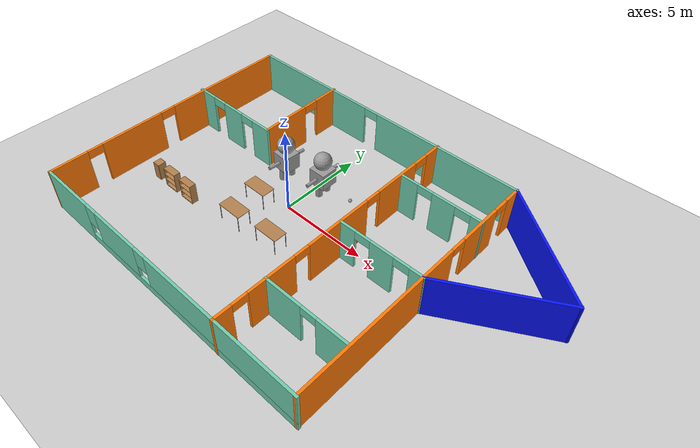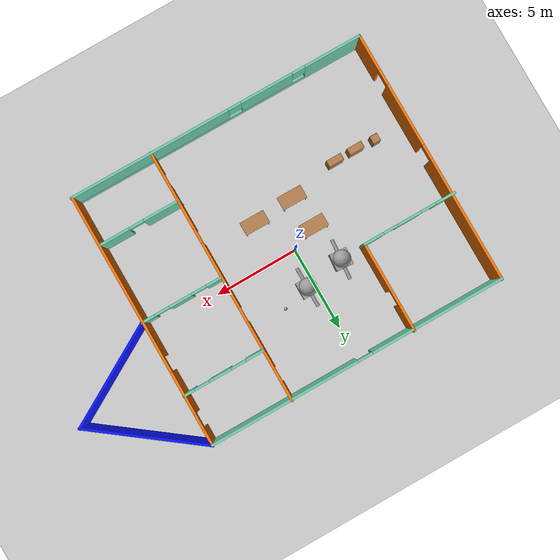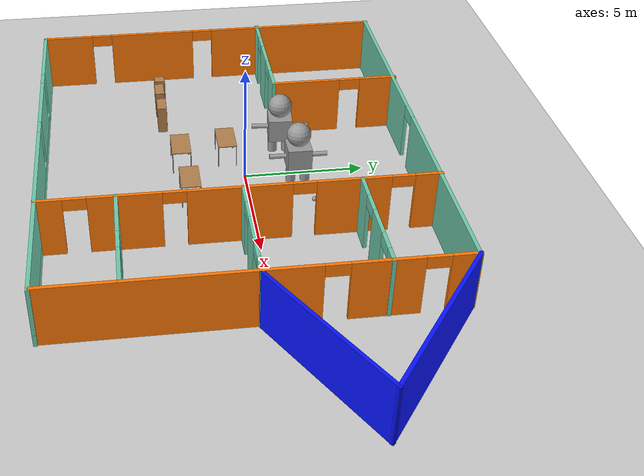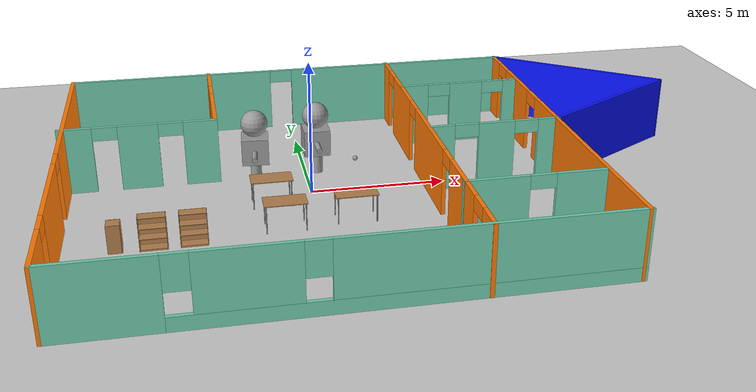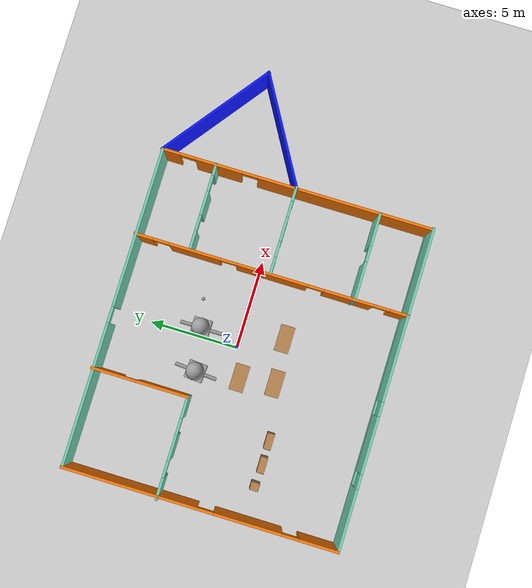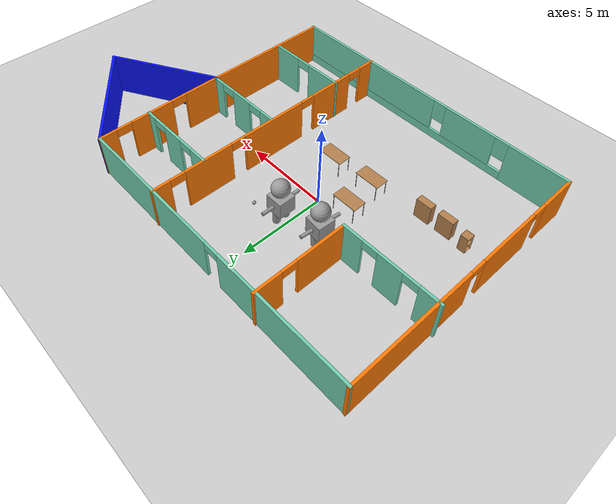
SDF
<sdf version="1.6">
 <world name="default">
  <plugin name="hello" filename="libhello.so"/>
  <light name="sun" type="directional">
   <pose>0 0 10 0 -0 0</pose>
   <diffuse>0.8 0.8 0.8 1</diffuse>
   <specular>0.2 0.2 0.2 1</specular>
   <attenuation>
    <range>1000</range>
    <constant>0.9</constant>
    <linear>0.01</linear>
    <quadratic>0.001</quadratic>
   </attenuation>
   <direction>-0.5 0.1 -0.9</direction>
  </light>
  <model name="ground_plane">
   <static>1</static>
   <link name="link">
    <collision name="collision">
     <geometry><plane><normal>0 0 1</normal><size>100 100</size></plane></geometry>
     <surface>
      <contact><collide_bitmask>65535</collide_bitmask></contact>
      <friction><ode><mu>100</mu><mu2>50</mu2></ode></friction>
     </surface>
    </collision>
    <visual name="visual">
     <cast_shadows>0</cast_shadows>
     <geometry><plane><normal>0 0 1</normal><size>100 100</size></plane></geometry>
     <material>
      <script><uri>file://media/materials/scripts/gazebo.material</uri><name>Gazebo/Grey</name></script>
     </material>
    </visual>
   </link>
  </model>
  <gravity>0 0 -9.8</gravity>
  <magnetic_field>6e-06 2.3e-05 -4.2e-05</magnetic_field>
  <atmosphere type="adiabatic"/>
  <physics name="default_physics" default="0" type="ode">
   <max_step_size>0.001</max_step_size>
   <real_time_factor>1</real_time_factor>
   <real_time_update_rate>1000</real_time_update_rate>
  </physics>
  <scene><ambient>0.4 0.4 0.4 1</ambient><background>0.7 0.7 0.7 1</background><shadows>1</shadows></scene>
  <spherical_coordinates>
   <surface_model>EARTH_WGS84</surface_model>
   <latitude_deg>0</latitude_deg>
   <longitude_deg>0</longitude_deg>
   <elevation>0</elevation>
   <heading_deg>0</heading_deg>
  </spherical_coordinates>
  <model name="Building">
   <pose>2.98663 -0.6582 0 0 -0 0</pose>
   <link name="Wall_0">
    <pose>-2.80813 7.61358 0 0 0 -0.001099</pose>
    <visual name="Wall_0_Visual_0">
     <pose>-4.97895 0 1.25 0 -0 0</pose>
     <geometry><box><size>8.08618 0.15 2.5</size></box></geometry>
     <material>
      <script><uri>file://media/materials/scripts/gazebo.material</uri><name>Gazebo/Grey</name></script>
      <ambient>0.435294 0.796078 0.67451 1</ambient>
     </material>
     <meta><layer>0</layer></meta>
    </visual>
    <collision name="Wall_0_Collision_0">
     <geometry><box><size>8.08618 0.15 2.5</size></box></geometry>
     <pose>-4.97895 0 1.25 0 -0 0</pose>
    </collision>
    <visual name="Wall_0_Visual_1">
     <pose>4.49309 0 1.25 0 -0 0</pose>
     <geometry><box><size>9.0579 0.15 2.5</size></box></geometry>
     <material>
      <script><uri>file://media/materials/scripts/gazebo.material</uri><name>Gazebo/Grey</name></script>
      <ambient>0.435294 0.796078 0.67451 1</ambient>
     </material>
     <meta><layer>0</layer></meta>
    </visual>
    <collision name="Wall_0_Collision_1">
     <geometry><box><size>9.0579 0.15 2.5</size></box></geometry>
     <pose>4.49309 0 1.25 0 -0 0</pose>
    </collision>
    <visual name="Wall_0_Visual_2">
     <pose>-0.485857 0 2.25 0 -0 0</pose>
     <geometry><box><size>0.9 0.15 0.5</size></box></geometry>
     <material>
      <script><uri>file://media/materials/scripts/gazebo.material</uri><name>Gazebo/Grey</name></script>
      <ambient>0.435294 0.796078 0.67451 1</ambient>
     </material>
     <meta><layer>0</layer></meta>
    </visual>
    <collision name="Wall_0_Collision_2">
     <geometry><box><size>0.9 0.15 0.5</size></box></geometry>
     <pose>-0.485857 0 2.25 0 -0 0</pose>
    </collision>
   </link>
   <link name="Wall_11">
    <pose>3.73817 4.58148 0 0 -0 0</pose>
    <visual name="Wall_11_Visual_0">
     <pose>-1.93324 0 1.25 0 -0 0</pose>
     <geometry><box><size>1.13352 0.15 2.5</size></box></geometry>
     <material>
      <script><uri>file://media/materials/scripts/gazebo.material</uri><name>Gazebo/Grey</name></script>
      <ambient>0.435294 0.796078 0.67451 1</ambient>
     </material>
     <meta><layer>0</layer></meta>
    </visual>
    <collision name="Wall_11_Collision_0">
     <geometry><box><size>1.13352 0.15 2.5</size></box></geometry>
     <pose>-1.93324 0 1.25 0 -0 0</pose>
    </collision>
    <visual name="Wall_11_Visual_1">
     <pose>0.209239 0 1.25 0 -0 0</pose>
     <geometry><box><size>1.35144 0.15 2.5</size></box></geometry>
     <material>
      <script><uri>file://media/materials/scripts/gazebo.material</uri><name>Gazebo/Grey</name></script>
      <ambient>0.435294 0.796078 0.67451 1</ambient>
     </material>
     <meta><layer>0</layer></meta>
    </visual>
    <collision name="Wall_11_Collision_1">
     <geometry><box><size>1.35144 0.15 2.5</size></box></geometry>
     <pose>0.209239 0 1.25 0 -0 0</pose>
    </collision>
    <visual name="Wall_11_Visual_2">
     <pose>2.14248 0 1.25 0 -0 0</pose>
     <geometry><box><size>0.71504 0.15 2.5</size></box></geometry>
     <material>
      <script><uri>file://media/materials/scripts/gazebo.material</uri><name>Gazebo/Grey</name></script>
      <ambient>0.435294 0.796078 0.67451 1</ambient>
     </material>
     <meta><layer>0</layer></meta>
    </visual>
    <collision name="Wall_11_Collision_2">
     <geometry><box><size>0.71504 0.15 2.5</size></box></geometry>
     <pose>2.14248 0 1.25 0 -0 0</pose>
    </collision>
    <visual name="Wall_11_Visual_3">
     <pose>-0.916481 0 2.25 0 -0 0</pose>
     <geometry><box><size>0.9 0.15 0.5</size></box></geometry>
     <material>
      <script><uri>file://media/materials/scripts/gazebo.material</uri><name>Gazebo/Grey</name></script>
      <ambient>0.435294 0.796078 0.67451 1</ambient>
     </material>
     <meta><layer>0</layer></meta>
    </visual>
    <collision name="Wall_11_Collision_3">
     <geometry><box><size>0.9 0.15 0.5</size></box></geometry>
     <pose>-0.916481 0 2.25 0 -0 0</pose>
    </collision>
    <visual name="Wall_11_Visual_4">
     <pose>1.33496 0 2.25 0 -0 0</pose>
     <geometry><box><size>0.9 0.15 0.5</size></box></geometry>
     <material>
      <script><uri>file://media/materials/scripts/gazebo.material</uri><name>Gazebo/Grey</name></script>
      <ambient>0.435294 0.796078 0.67451 1</ambient>
     </material>
     <meta><layer>0</layer></meta>
    </visual>
    <collision name="Wall_11_Collision_4">
     <geometry><box><size>0.9 0.15 0.5</size></box></geometry>
     <pose>1.33496 0 2.25 0 -0 0</pose>
    </collision>
   </link>
   <link name="Wall_13">
    <pose>3.77862 0.050456 0 0 -0 0</pose>
    <visual name="Wall_13_Visual_0">
     <pose>-2.02383 0 1.25 0 -0 0</pose>
     <geometry><box><size>0.952349 0.15 2.5</size></box></geometry>
     <material>
      <script><uri>file://media/materials/scripts/gazebo.material</uri><name>Gazebo/Grey</name></script>
      <ambient>0.435294 0.796078 0.67451 1</ambient>
     </material>
     <meta><layer>0</layer></meta>
    </visual>
    <collision name="Wall_13_Collision_0">
     <geometry><box><size>0.952349 0.15 2.5</size></box></geometry>
     <pose>-2.02383 0 1.25 0 -0 0</pose>
    </collision>
    <visual name="Wall_13_Visual_1">
     <pose>0.041638 0 1.25 0 -0 0</pose>
     <geometry><box><size>1.37858 0.15 2.5</size></box></geometry>
     <material>
      <script><uri>file://media/materials/scripts/gazebo.material</uri><name>Gazebo/Grey</name></script>
      <ambient>0.435294 0.796078 0.67451 1</ambient>
     </material>
     <meta><layer>0</layer></meta>
    </visual>
    <collision name="Wall_13_Collision_1">
     <geometry><box><size>1.37858 0.15 2.5</size></box></geometry>
     <pose>0.041638 0 1.25 0 -0 0</pose>
    </collision>
    <visual name="Wall_13_Visual_2">
     <pose>2.06546 0 1.25 0 -0 0</pose>
     <geometry><box><size>0.869072 0.15 2.5</size></box></geometry>
     <material>
      <script><uri>file://media/materials/scripts/gazebo.material</uri><name>Gazebo/Grey</name></script>
      <ambient>0.435294 0.796078 0.67451 1</ambient>
     </material>
     <meta><layer>0</layer></meta>
    </visual>
    <collision name="Wall_13_Collision_2">
     <geometry><box><size>0.869072 0.15 2.5</size></box></geometry>
     <pose>2.06546 0 1.25 0 -0 0</pose>
    </collision>
    <visual name="Wall_13_Visual_3">
     <pose>-1.09765 0 2.25 0 -0 0</pose>
     <geometry><box><size>0.9 0.15 0.5</size></box></geometry>
     <material>
      <script><uri>file://media/materials/scripts/gazebo.material</uri><name>Gazebo/Grey</name></script>
      <ambient>0.435294 0.796078 0.67451 1</ambient>
     </material>
     <meta><layer>0</layer></meta>
    </visual>
    <collision name="Wall_13_Collision_3">
     <geometry><box><size>0.9 0.15 0.5</size></box></geometry>
     <pose>-1.09765 0 2.25 0 -0 0</pose>
    </collision>
    <visual name="Wall_13_Visual_4">
     <pose>1.18093 0 2.25 0 -0 0</pose>
     <geometry><box><size>0.9 0.15 0.5</size></box></geometry>
     <material>
      <script><uri>file://media/materials/scripts/gazebo.material</uri><name>Gazebo/Grey</name></script>
      <ambient>0.435294 0.796078 0.67451 1</ambient>
     </material>
     <meta><layer>0</layer></meta>
    </visual>
    <collision name="Wall_13_Collision_4">
     <geometry><box><size>0.9 0.15 0.5</size></box></geometry>
     <pose>1.18093 0 2.25 0 -0 0</pose>
    </collision>
   </link>
   <link name="Wall_15">
    <pose>3.67214 -4.70387 0 0 -0 0</pose>
    <visual name="Wall_15_Visual_0">
     <pose>-1.37973 0 1.25 0 -0 0</pose>
     <geometry><box><size>2.24055 0.15 2.5</size></box></geometry>
     <material>
      <script><uri>file://media/materials/scripts/gazebo.material</uri><name>Gazebo/Grey</name></script>
      <ambient>0.435294 0.796078 0.67451 1</ambient>
     </material>
     <meta><layer>0</layer></meta>
    </visual>
    <collision name="Wall_15_Collision_0">
     <geometry><box><size>2.24055 0.15 2.5</size></box></geometry>
     <pose>-1.37973 0 1.25 0 -0 0</pose>
    </collision>
    <visual name="Wall_15_Visual_1">
     <pose>1.57028 0 1.25 0 -0 0</pose>
     <geometry><box><size>1.85945 0.15 2.5</size></box></geometry>
     <material>
      <script><uri>file://media/materials/scripts/gazebo.material</uri><name>Gazebo/Grey</name></script>
      <ambient>0.435294 0.796078 0.67451 1</ambient>
     </material>
     <meta><layer>0</layer></meta>
    </visual>
    <collision name="Wall_15_Collision_1">
     <geometry><box><size>1.85945 0.15 2.5</size></box></geometry>
     <pose>1.57028 0 1.25 0 -0 0</pose>
    </collision>
    <visual name="Wall_15_Visual_2">
     <pose>0.190549 0 2.25 0 -0 0</pose>
     <geometry><box><size>0.9 0.15 0.5</size></box></geometry>
     <material>
      <script><uri>file://media/materials/scripts/gazebo.material</uri><name>Gazebo/Grey</name></script>
      <ambient>0.435294 0.796078 0.67451 1</ambient>
     </material>
     <meta><layer>0</layer></meta>
    </visual>
    <collision name="Wall_15_Collision_2">
     <geometry><box><size>0.9 0.15 0.5</size></box></geometry>
     <pose>0.190549 0 2.25 0 -0 0</pose>
    </collision>
   </link>
   <link name="Wall_17">
    <collision name="Wall_17_Collision">
     <geometry><box><size>6.75 0.15 2.5</size></box></geometry>
     <pose>0 0 1.25 0 -0 0</pose>
    </collision>
    <visual name="Wall_17_Visual">
     <pose>0 0 1.25 0 -0 0</pose>
     <geometry><box><size>6.75 0.15 2.5</size></box></geometry>
     <material>
      <script><uri>file://media/materials/scripts/gazebo.material</uri><name>Gazebo/Grey</name></script>
      <ambient>0.0313726 0.0784314 1 1</ambient>
     </material>
     <meta><layer>0</layer></meta>
    </visual>
    <pose>9.00455 1.66326 0 0 -0 0.523599</pose>
   </link>
   <link name="Wall_18">
    <collision name="Wall_18_Collision">
     <geometry><box><size>7.31911 0.15 2.5</size></box></geometry>
     <pose>0 0 1.25 0 -0 0</pose>
    </collision>
    <visual name="Wall_18_Visual">
     <pose>0 0 1.25 0 -0 0</pose>
     <geometry><box><size>7.31911 0.15 2.5</size></box></geometry>
     <material>
      <script><uri>file://media/materials/scripts/gazebo.material</uri><name>Gazebo/Grey</name></script>
      <ambient>0.0313726 0.0784314 1 1</ambient>
     </material>
     <meta><layer>0</layer></meta>
    </visual>
    <pose>9.00067 5.47181 0 0 -0 2.49536</pose>
   </link>
   <link name="Wall_2">
    <pose>-11.7501 0.006796 0 0 0 -1.57013</pose>
    <visual name="Wall_2_Visual_0">
     <pose>-3.93136 0 1.25 0 -0 0</pose>
     <geometry><box><size>7.57372 0.15 2.5</size></box></geometry>
     <material>
      <script><uri>file://media/materials/scripts/gazebo.material</uri><name>Gazebo/Grey</name></script>
      <ambient>0.996078 0.47451 0.0196078 1</ambient>
     </material>
     <meta><layer>0</layer></meta>
    </visual>
    <collision name="Wall_2_Collision_0">
     <geometry><box><size>7.57372 0.15 2.5</size></box></geometry>
     <pose>-3.93136 0 1.25 0 -0 0</pose>
    </collision>
    <visual name="Wall_2_Visual_1">
     <pose>2.66282 0 1.25 0 -0 0</pose>
     <geometry><box><size>3.81463 0.15 2.5</size></box></geometry>
     <material>
      <script><uri>file://media/materials/scripts/gazebo.material</uri><name>Gazebo/Grey</name></script>
      <ambient>0.996078 0.47451 0.0196078 1</ambient>
     </material>
     <meta><layer>0</layer></meta>
    </visual>
    <collision name="Wall_2_Collision_1">
     <geometry><box><size>3.81463 0.15 2.5</size></box></geometry>
     <pose>2.66282 0 1.25 0 -0 0</pose>
    </collision>
    <visual name="Wall_2_Visual_2">
     <pose>6.59418 0 1.25 0 -0 0</pose>
     <geometry><box><size>2.24808 0.15 2.5</size></box></geometry>
     <material>
      <script><uri>file://media/materials/scripts/gazebo.material</uri><name>Gazebo/Grey</name></script>
      <ambient>0.996078 0.47451 0.0196078 1</ambient>
     </material>
     <meta><layer>0</layer></meta>
    </visual>
    <collision name="Wall_2_Collision_2">
     <geometry><box><size>2.24808 0.15 2.5</size></box></geometry>
     <pose>6.59418 0 1.25 0 -0 0</pose>
    </collision>
    <visual name="Wall_2_Visual_3">
     <pose>0.305505 0 2.25 0 -0 0</pose>
     <geometry><box><size>0.9 0.15 0.5</size></box></geometry>
     <material>
      <script><uri>file://media/materials/scripts/gazebo.material</uri><name>Gazebo/Grey</name></script>
      <ambient>0.996078 0.47451 0.0196078 1</ambient>
     </material>
     <meta><layer>0</layer></meta>
    </visual>
    <collision name="Wall_2_Collision_3">
     <geometry><box><size>0.9 0.15 0.5</size></box></geometry>
     <pose>0.305505 0 2.25 0 -0 0</pose>
    </collision>
    <visual name="Wall_2_Visual_4">
     <pose>5.02014 0 2.25 0 -0 0</pose>
     <geometry><box><size>0.9 0.15 0.5</size></box></geometry>
     <material>
      <script><uri>file://media/materials/scripts/gazebo.material</uri><name>Gazebo/Grey</name></script>
      <ambient>0.996078 0.47451 0.0196078 1</ambient>
     </material>
     <meta><layer>0</layer></meta>
    </visual>
    <collision name="Wall_2_Collision_4">
     <geometry><box><size>0.9 0.15 0.5</size></box></geometry>
     <pose>5.02014 0 2.25 0 -0 0</pose>
    </collision>
   </link>
   <link name="Wall_3">
    <pose>-2.75147 -7.66637 0 0 0 -0.003347</pose>
    <visual name="Wall_3_Visual_0">
     <pose>-7.29617 0 1.25 0 -0 0</pose>
     <geometry><box><size>3.45183 0.15 2.5</size></box></geometry>
     <material>
      <script><uri>file://media/materials/scripts/gazebo.material</uri><name>Gazebo/Grey</name></script>
      <ambient>0.435294 0.796078 0.67451 1</ambient>
     </material>
     <meta><layer>0</layer></meta>
    </visual>
    <collision name="Wall_3_Collision_0">
     <geometry><box><size>3.45183 0.15 2.5</size></box></geometry>
     <pose>-7.29617 0 1.25 0 -0 0</pose>
    </collision>
    <visual name="Wall_3_Visual_1">
     <pose>1.72591 0 0.25 0 -0 0</pose>
     <geometry><box><size>14.5923 0.15 0.5</size></box></geometry>
     <material>
      <script><uri>file://media/materials/scripts/gazebo.material</uri><name>Gazebo/Grey</name></script>
      <ambient>0.435294 0.796078 0.67451 1</ambient>
     </material>
     <meta><layer>0</layer></meta>
    </visual>
    <collision name="Wall_3_Collision_1">
     <geometry><box><size>14.5923 0.15 0.5</size></box></geometry>
     <pose>1.72591 0 0.25 0 -0 0</pose>
    </collision>
    <visual name="Wall_3_Visual_2">
     <pose>-3.16851 0 1.5 0 -0 0</pose>
     <geometry><box><size>3.2035 0.15 2</size></box></geometry>
     <material>
      <script><uri>file://media/materials/scripts/gazebo.material</uri><name>Gazebo/Grey</name></script>
      <ambient>0.435294 0.796078 0.67451 1</ambient>
     </material>
     <meta><layer>0</layer></meta>
    </visual>
    <collision name="Wall_3_Collision_2">
     <geometry><box><size>3.2035 0.15 2</size></box></geometry>
     <pose>-3.16851 0 1.5 0 -0 0</pose>
    </collision>
    <visual name="Wall_3_Visual_3">
     <pose>4.12766 0 1.5 0 -0 0</pose>
     <geometry><box><size>9.78884 0.15 2</size></box></geometry>
     <material>
      <script><uri>file://media/materials/scripts/gazebo.material</uri><name>Gazebo/Grey</name></script>
      <ambient>0.435294 0.796078 0.67451 1</ambient>
     </material>
     <meta><layer>0</layer></meta>
    </visual>
    <collision name="Wall_3_Collision_3">
     <geometry><box><size>9.78884 0.15 2</size></box></geometry>
     <pose>4.12766 0 1.5 0 -0 0</pose>
    </collision>
    <visual name="Wall_3_Visual_4">
     <pose>-5.17026 0 1.9 0 -0 0</pose>
     <geometry><box><size>0.8 0.15 1.2</size></box></geometry>
     <material>
      <script><uri>file://media/materials/scripts/gazebo.material</uri><name>Gazebo/Grey</name></script>
      <ambient>0.435294 0.796078 0.67451 1</ambient>
     </material>
     <meta><layer>0</layer></meta>
    </visual>
    <collision name="Wall_3_Collision_4">
     <geometry><box><size>0.8 0.15 1.2</size></box></geometry>
     <pose>-5.17026 0 1.9 0 -0 0</pose>
    </collision>
    <visual name="Wall_3_Visual_5">
     <pose>-1.16676 0 1.9 0 -0 0</pose>
     <geometry><box><size>0.8 0.15 1.2</size></box></geometry>
     <material>
      <script><uri>file://media/materials/scripts/gazebo.material</uri><name>Gazebo/Grey</name></script>
      <ambient>0.435294 0.796078 0.67451 1</ambient>
     </material>
     <meta><layer>0</layer></meta>
    </visual>
    <collision name="Wall_3_Collision_5">
     <geometry><box><size>0.8 0.15 1.2</size></box></geometry>
     <pose>-1.16676 0 1.9 0 -0 0</pose>
    </collision>
   </link>
   <link name="Wall_4">
    <pose>6.14398 -0.032979 0 0 -0 1.57146</pose>
    <visual name="Wall_4_Visual_0">
     <pose>-2.74852 0 1.25 0 -0 0</pose>
     <geometry><box><size>9.97962 0.15 2.5</size></box></geometry>
     <material>
      <script><uri>file://media/materials/scripts/gazebo.material</uri><name>Gazebo/Grey</name></script>
      <ambient>0.996078 0.47451 0.0196078 1</ambient>
     </material>
     <meta><layer>0</layer></meta>
    </visual>
    <collision name="Wall_4_Collision_0">
     <geometry><box><size>9.97962 0.15 2.5</size></box></geometry>
     <pose>-2.74852 0 1.25 0 -0 0</pose>
    </collision>
    <visual name="Wall_4_Visual_1">
     <pose>4.45026 0 1.25 0 -0 0</pose>
     <geometry><box><size>2.61795 0.15 2.5</size></box></geometry>
     <material>
      <script><uri>file://media/materials/scripts/gazebo.material</uri><name>Gazebo/Grey</name></script>
      <ambient>0.996078 0.47451 0.0196078 1</ambient>
     </material>
     <meta><layer>0</layer></meta>
    </visual>
    <collision name="Wall_4_Collision_1">
     <geometry><box><size>2.61795 0.15 2.5</size></box></geometry>
     <pose>4.45026 0 1.25 0 -0 0</pose>
    </collision>
    <visual name="Wall_4_Visual_2">
     <pose>7.19878 0 1.25 0 -0 0</pose>
     <geometry><box><size>1.0791 0.15 2.5</size></box></geometry>
     <material>
      <script><uri>file://media/materials/scripts/gazebo.material</uri><name>Gazebo/Grey</name></script>
      <ambient>0.996078 0.47451 0.0196078 1</ambient>
     </material>
     <meta><layer>0</layer></meta>
    </visual>
    <collision name="Wall_4_Collision_2">
     <geometry><box><size>1.0791 0.15 2.5</size></box></geometry>
     <pose>7.19878 0 1.25 0 -0 0</pose>
    </collision>
    <visual name="Wall_4_Visual_3">
     <pose>2.69129 0 2.25 0 -0 0</pose>
     <geometry><box><size>0.9 0.15 0.5</size></box></geometry>
     <material>
      <script><uri>file://media/materials/scripts/gazebo.material</uri><name>Gazebo/Grey</name></script>
      <ambient>0.996078 0.47451 0.0196078 1</ambient>
     </material>
     <meta><layer>0</layer></meta>
    </visual>
    <collision name="Wall_4_Collision_3">
     <geometry><box><size>0.9 0.15 0.5</size></box></geometry>
     <pose>2.69129 0 2.25 0 -0 0</pose>
    </collision>
    <visual name="Wall_4_Visual_4">
     <pose>6.20924 0 2.25 0 -0 0</pose>
     <geometry><box><size>0.9 0.15 0.5</size></box></geometry>
     <material>
      <script><uri>file://media/materials/scripts/gazebo.material</uri><name>Gazebo/Grey</name></script>
      <ambient>0.996078 0.47451 0.0196078 1</ambient>
     </material>
     <meta><layer>0</layer></meta>
    </visual>
    <collision name="Wall_4_Collision_4">
     <geometry><box><size>0.9 0.15 0.5</size></box></geometry>
     <pose>6.20924 0 2.25 0 -0 0</pose>
    </collision>
   </link>
   <link name="Wall_6">
    <pose>-6.29248 5.02156 0 0 0 -1.5708</pose>
    <visual name="Wall_6_Visual_0">
     <pose>-1.93476 0 1.25 0 -0 0</pose>
     <geometry><box><size>1.63049 0.15 2.5</size></box></geometry>
     <material>
      <script><uri>file://media/materials/scripts/gazebo.material</uri><name>Gazebo/Grey</name></script>
      <ambient>0.996078 0.47451 0.0196078 1</ambient>
     </material>
     <meta><layer>0</layer></meta>
    </visual>
    <collision name="Wall_6_Collision_0">
     <geometry><box><size>1.63049 0.15 2.5</size></box></geometry>
     <pose>-1.93476 0 1.25 0 -0 0</pose>
    </collision>
    <visual name="Wall_6_Visual_1">
     <pose>1.26524 0 1.25 0 -0 0</pose>
     <geometry><box><size>2.96951 0.15 2.5</size></box></geometry>
     <material>
      <script><uri>file://media/materials/scripts/gazebo.material</uri><name>Gazebo/Grey</name></script>
      <ambient>0.996078 0.47451 0.0196078 1</ambient>
     </material>
     <meta><layer>0</layer></meta>
    </visual>
    <collision name="Wall_6_Collision_1">
     <geometry><box><size>2.96951 0.15 2.5</size></box></geometry>
     <pose>1.26524 0 1.25 0 -0 0</pose>
    </collision>
    <visual name="Wall_6_Visual_2">
     <pose>-0.669512 0 2.25 0 -0 0</pose>
     <geometry><box><size>0.9 0.15 0.5</size></box></geometry>
     <material>
      <script><uri>file://media/materials/scripts/gazebo.material</uri><name>Gazebo/Grey</name></script>
      <ambient>0.996078 0.47451 0.0196078 1</ambient>
     </material>
     <meta><layer>0</layer></meta>
    </visual>
    <collision name="Wall_6_Collision_2">
     <geometry><box><size>0.9 0.15 0.5</size></box></geometry>
     <pose>-0.669512 0 2.25 0 -0 0</pose>
    </collision>
   </link>
   <link name="Wall_7">
    <pose>-9.09248 2.34656 0 0 -0 3.14159</pose>
    <visual name="Wall_7_Visual_0">
     <pose>-2.24817 0 1.25 0 -0 0</pose>
     <geometry><box><size>1.25366 0.15 2.5</size></box></geometry>
     <material>
      <script><uri>file://media/materials/scripts/gazebo.material</uri><name>Gazebo/Grey</name></script>
      <ambient>0.435294 0.796078 0.67451 1</ambient>
     </material>
     <meta><layer>0</layer></meta>
    </visual>
    <collision name="Wall_7_Collision_0">
     <geometry><box><size>1.25366 0.15 2.5</size></box></geometry>
     <pose>-2.24817 0 1.25 0 -0 0</pose>
    </collision>
    <visual name="Wall_7_Visual_1">
     <pose>0.006381 0 1.25 0 -0 0</pose>
     <geometry><box><size>1.45545 0.15 2.5</size></box></geometry>
     <material>
      <script><uri>file://media/materials/scripts/gazebo.material</uri><name>Gazebo/Grey</name></script>
      <ambient>0.435294 0.796078 0.67451 1</ambient>
     </material>
     <meta><layer>0</layer></meta>
    </visual>
    <collision name="Wall_7_Collision_1">
     <geometry><box><size>1.45545 0.15 2.5</size></box></geometry>
     <pose>0.006381 0 1.25 0 -0 0</pose>
    </collision>
    <visual name="Wall_7_Visual_2">
     <pose>2.25455 0 1.25 0 -0 0</pose>
     <geometry><box><size>1.2409 0.15 2.5</size></box></geometry>
     <material>
      <script><uri>file://media/materials/scripts/gazebo.material</uri><name>Gazebo/Grey</name></script>
      <ambient>0.435294 0.796078 0.67451 1</ambient>
     </material>
     <meta><layer>0</layer></meta>
    </visual>
    <collision name="Wall_7_Collision_2">
     <geometry><box><size>1.2409 0.15 2.5</size></box></geometry>
     <pose>2.25455 0 1.25 0 -0 0</pose>
    </collision>
    <visual name="Wall_7_Visual_3">
     <pose>-1.17134 0 2.25 0 -0 0</pose>
     <geometry><box><size>0.9 0.15 0.5</size></box></geometry>
     <material>
      <script><uri>file://media/materials/scripts/gazebo.material</uri><name>Gazebo/Grey</name></script>
      <ambient>0.435294 0.796078 0.67451 1</ambient>
     </material>
     <meta><layer>0</layer></meta>
    </visual>
    <collision name="Wall_7_Collision_3">
     <geometry><box><size>0.9 0.15 0.5</size></box></geometry>
     <pose>-1.17134 0 2.25 0 -0 0</pose>
    </collision>
    <visual name="Wall_7_Visual_4">
     <pose>1.1841 0 2.25 0 -0 0</pose>
     <geometry><box><size>0.9 0.15 0.5</size></box></geometry>
     <material>
      <script><uri>file://media/materials/scripts/gazebo.material</uri><name>Gazebo/Grey</name></script>
      <ambient>0.435294 0.796078 0.67451 1</ambient>
     </material>
     <meta><layer>0</layer></meta>
    </visual>
    <collision name="Wall_7_Collision_4">
     <geometry><box><size>0.9 0.15 0.5</size></box></geometry>
     <pose>1.1841 0 2.25 0 -0 0</pose>
    </collision>
   </link>
   <link name="Wall_9">
    <pose>1.27271 -0.018895 0 0 0 -1.5708</pose>
    <visual name="Wall_9_Visual_0">
     <pose>-7.19971 0 1.25 0 -0 0</pose>
     <geometry><box><size>1.10059 0.15 2.5</size></box></geometry>
     <material>
      <script><uri>file://media/materials/scripts/gazebo.material</uri><name>Gazebo/Grey</name></script>
      <ambient>0.996078 0.47451 0.0196078 1</ambient>
     </material>
     <meta><layer>0</layer></meta>
    </visual>
    <collision name="Wall_9_Collision_0">
     <geometry><box><size>1.10059 0.15 2.5</size></box></geometry>
     <pose>-7.19971 0 1.25 0 -0 0</pose>
    </collision>
    <visual name="Wall_9_Visual_1">
     <pose>-4.30282 0 1.25 0 -0 0</pose>
     <geometry><box><size>2.89319 0.15 2.5</size></box></geometry>
     <material>
      <script><uri>file://media/materials/scripts/gazebo.material</uri><name>Gazebo/Grey</name></script>
      <ambient>0.996078 0.47451 0.0196078 1</ambient>
     </material>
     <meta><layer>0</layer></meta>
    </visual>
    <collision name="Wall_9_Collision_1">
     <geometry><box><size>2.89319 0.15 2.5</size></box></geometry>
     <pose>-4.30282 0 1.25 0 -0 0</pose>
    </collision>
    <visual name="Wall_9_Visual_2">
     <pose>0.049995 0 1.25 0 -0 0</pose>
     <geometry><box><size>4.01244 0.15 2.5</size></box></geometry>
     <material>
      <script><uri>file://media/materials/scripts/gazebo.material</uri><name>Gazebo/Grey</name></script>
      <ambient>0.996078 0.47451 0.0196078 1</ambient>
     </material>
     <meta><layer>0</layer></meta>
    </visual>
    <collision name="Wall_9_Collision_2">
     <geometry><box><size>4.01244 0.15 2.5</size></box></geometry>
     <pose>0.049995 0 1.25 0 -0 0</pose>
    </collision>
    <visual name="Wall_9_Visual_3">
     <pose>4.35692 0 1.25 0 -0 0</pose>
     <geometry><box><size>2.80142 0.15 2.5</size></box></geometry>
     <material>
      <script><uri>file://media/materials/scripts/gazebo.material</uri><name>Gazebo/Grey</name></script>
      <ambient>0.996078 0.47451 0.0196078 1</ambient>
     </material>
     <meta><layer>0</layer></meta>
    </visual>
    <collision name="Wall_9_Collision_3">
     <geometry><box><size>2.80142 0.15 2.5</size></box></geometry>
     <pose>4.35692 0 1.25 0 -0 0</pose>
    </collision>
    <visual name="Wall_9_Visual_4">
     <pose>7.20381 0 1.25 0 -0 0</pose>
     <geometry><box><size>1.09237 0.15 2.5</size></box></geometry>
     <material>
      <script><uri>file://media/materials/scripts/gazebo.material</uri><name>Gazebo/Grey</name></script>
      <ambient>0.996078 0.47451 0.0196078 1</ambient>
     </material>
     <meta><layer>0</layer></meta>
    </visual>
    <collision name="Wall_9_Collision_4">
     <geometry><box><size>1.09237 0.15 2.5</size></box></geometry>
     <pose>7.20381 0 1.25 0 -0 0</pose>
    </collision>
    <visual name="Wall_9_Visual_5">
     <pose>-6.19941 0 2.25 0 -0 0</pose>
     <geometry><box><size>0.9 0.15 0.5</size></box></geometry>
     <material>
      <script><uri>file://media/materials/scripts/gazebo.material</uri><name>Gazebo/Grey</name></script>
      <ambient>0.996078 0.47451 0.0196078 1</ambient>
     </material>
     <meta><layer>0</layer></meta>
    </visual>
    <collision name="Wall_9_Collision_5">
     <geometry><box><size>0.9 0.15 0.5</size></box></geometry>
     <pose>-6.19941 0 2.25 0 -0 0</pose>
    </collision>
    <visual name="Wall_9_Visual_6">
     <pose>-2.40622 0 2.25 0 -0 0</pose>
     <geometry><box><size>0.9 0.15 0.5</size></box></geometry>
     <material>
      <script><uri>file://media/materials/scripts/gazebo.material</uri><name>Gazebo/Grey</name></script>
      <ambient>0.996078 0.47451 0.0196078 1</ambient>
     </material>
     <meta><layer>0</layer></meta>
    </visual>
    <collision name="Wall_9_Collision_6">
     <geometry><box><size>0.9 0.15 0.5</size></box></geometry>
     <pose>-2.40622 0 2.25 0 -0 0</pose>
    </collision>
    <visual name="Wall_9_Visual_7">
     <pose>2.50621 0 2.25 0 -0 0</pose>
     <geometry><box><size>0.9 0.15 0.5</size></box></geometry>
     <material>
      <script><uri>file://media/materials/scripts/gazebo.material</uri><name>Gazebo/Grey</name></script>
      <ambient>0.996078 0.47451 0.0196078 1</ambient>
     </material>
     <meta><layer>0</layer></meta>
    </visual>
    <collision name="Wall_9_Collision_7">
     <geometry><box><size>0.9 0.15 0.5</size></box></geometry>
     <pose>2.50621 0 2.25 0 -0 0</pose>
    </collision>
    <visual name="Wall_9_Visual_8">
     <pose>6.20763 0 2.25 0 -0 0</pose>
     <geometry><box><size>0.9 0.15 0.5</size></box></geometry>
     <material>
      <script><uri>file://media/materials/scripts/gazebo.material</uri><name>Gazebo/Grey</name></script>
      <ambient>0.996078 0.47451 0.0196078 1</ambient>
     </material>
     <meta><layer>0</layer></meta>
    </visual>
    <collision name="Wall_9_Collision_8">
     <geometry><box><size>0.9 0.15 0.5</size></box></geometry>
     <pose>6.20763 0 2.25 0 -0 0</pose>
    </collision>
   </link>
   <static>1</static>
  </model>
  <model name="table">
   <static>1</static>
   <link name="link">
    <collision name="surface">
     <pose>0 0 1 0 -0 0</pose>
     <geometry><box><size>1.5 0.8 0.03</size></box></geometry>
     <surface><friction><ode><mu>0.6</mu><mu2>0.6</mu2></ode></friction></surface>
    </collision>
    <visual name="visual1">
     <pose>0 0 1 0 -0 0</pose>
     <geometry><box><size>1.5 0.8 0.03</size></box></geometry>
     <material>
      <script><uri>file://media/materials/scripts/gazebo.material</uri><name>Gazebo/Wood</name></script>
     </material>
    </visual>
    <collision name="front_left_leg">
     <pose>0.68 0.38 0.5 0 -0 0</pose>
     <geometry><cylinder><radius>0.02</radius><length>1</length></cylinder></geometry>
    </collision>
    <visual name="front_left_leg">
     <pose>0.68 0.38 0.5 0 -0 0</pose>
     <geometry><cylinder><radius>0.02</radius><length>1</length></cylinder></geometry>
     <material>
      <script><uri>file://media/materials/scripts/gazebo.material</uri><name>Gazebo/Grey</name></script>
     </material>
    </visual>
    <collision name="front_right_leg">
     <pose>0.68 -0.38 0.5 0 -0 0</pose>
     <geometry><cylinder><radius>0.02</radius><length>1</length></cylinder></geometry>
    </collision>
    <visual name="front_right_leg">
     <pose>0.68 -0.38 0.5 0 -0 0</pose>
     <geometry><cylinder><radius>0.02</radius><length>1</length></cylinder></geometry>
     <material>
      <script><uri>file://media/materials/scripts/gazebo.material</uri><name>Gazebo/Grey</name></script>
     </material>
    </visual>
    <collision name="back_right_leg">
     <pose>-0.68 -0.38 0.5 0 -0 0</pose>
     <geometry><cylinder><radius>0.02</radius><length>1</length></cylinder></geometry>
    </collision>
    <visual name="back_right_leg">
     <pose>-0.68 -0.38 0.5 0 -0 0</pose>
     <geometry><cylinder><radius>0.02</radius><length>1</length></cylinder></geometry>
     <material>
      <script><uri>file://media/materials/scripts/gazebo.material</uri><name>Gazebo/Grey</name></script>
     </material>
    </visual>
    <collision name="back_left_leg">
     <pose>-0.68 0.38 0.5 0 -0 0</pose>
     <geometry><cylinder><radius>0.02</radius><length>1</length></cylinder></geometry>
    </collision>
    <visual name="back_left_leg">
     <pose>-0.68 0.38 0.5 0 -0 0</pose>
     <geometry><cylinder><radius>0.02</radius><length>1</length></cylinder></geometry>
     <material>
      <script><uri>file://media/materials/scripts/gazebo.material</uri><name>Gazebo/Grey</name></script>
     </material>
    </visual>
   </link>
   <pose>-1.26954 -2.58897 0 0 -0 0</pose>
  </model>
  <model name="table_0">
   <static>1</static>
   <link name="link">
    <collision name="surface">
     <pose>0 0 1 0 -0 0</pose>
     <geometry><box><size>1.5 0.8 0.03</size></box></geometry>
     <surface><friction><ode><mu>0.6</mu><mu2>0.6</mu2></ode></friction></surface>
    </collision>
    <visual name="visual1">
     <pose>0 0 1 0 -0 0</pose>
     <geometry><box><size>1.5 0.8 0.03</size></box></geometry>
     <material>
      <script><uri>file://media/materials/scripts/gazebo.material</uri><name>Gazebo/Wood</name></script>
     </material>
    </visual>
    <collision name="front_left_leg">
     <pose>0.68 0.38 0.5 0 -0 0</pose>
     <geometry><cylinder><radius>0.02</radius><length>1</length></cylinder></geometry>
    </collision>
    <visual name="front_left_leg">
     <pose>0.68 0.38 0.5 0 -0 0</pose>
     <geometry><cylinder><radius>0.02</radius><length>1</length></cylinder></geometry>
     <material>
      <script><uri>file://media/materials/scripts/gazebo.material</uri><name>Gazebo/Grey</name></script>
     </material>
    </visual>
    <collision name="front_right_leg">
     <pose>0.68 -0.38 0.5 0 -0 0</pose>
     <geometry><cylinder><radius>0.02</radius><length>1</length></cylinder></geometry>
    </collision>
    <visual name="front_right_leg">
     <pose>0.68 -0.38 0.5 0 -0 0</pose>
     <geometry><cylinder><radius>0.02</radius><length>1</length></cylinder></geometry>
     <material>
      <script><uri>file://media/materials/scripts/gazebo.material</uri><name>Gazebo/Grey</name></script>
     </material>
    </visual>
    <collision name="back_right_leg">
     <pose>-0.68 -0.38 0.5 0 -0 0</pose>
     <geometry><cylinder><radius>0.02</radius><length>1</length></cylinder></geometry>
    </collision>
    <visual name="back_right_leg">
     <pose>-0.68 -0.38 0.5 0 -0 0</pose>
     <geometry><cylinder><radius>0.02</radius><length>1</length></cylinder></geometry>
     <material>
      <script><uri>file://media/materials/scripts/gazebo.material</uri><name>Gazebo/Grey</name></script>
     </material>
    </visual>
    <collision name="back_left_leg">
     <pose>-0.68 0.38 0.5 0 -0 0</pose>
     <geometry><cylinder><radius>0.02</radius><length>1</length></cylinder></geometry>
    </collision>
    <visual name="back_left_leg">
     <pose>-0.68 0.38 0.5 0 -0 0</pose>
     <geometry><cylinder><radius>0.02</radius><length>1</length></cylinder></geometry>
     <material>
      <script><uri>file://media/materials/scripts/gazebo.material</uri><name>Gazebo/Grey</name></script>
     </material>
    </visual>
   </link>
   <pose>1.21649 -2.39679 0 0 -0 0</pose>
  </model>
  <model name="bookshelf">
   <static>1</static>
   <link name="link">
    <inertial><mass>1</mass></inertial>
    <collision name="back">
     <pose>0 0.005 0.6 0 -0 0</pose>
     <geometry><box><size>0.9 0.01 1.2</size></box></geometry>
    </collision>
    <visual name="visual1">
     <pose>0 0.005 0.6 0 -0 0</pose>
     <geometry><box><size>0.9 0.01 1.2</size></box></geometry>
     <material>
      <script><uri>file://media/materials/scripts/gazebo.material</uri><name>Gazebo/Wood</name></script>
     </material>
    </visual>
    <collision name="left_side">
     <pose>0.45 -0.195 0.6 0 -0 0</pose>
     <geometry><box><size>0.02 0.4 1.2</size></box></geometry>
    </collision>
    <visual name="visual2">
     <pose>0.45 -0.195 0.6 0 -0 0</pose>
     <geometry><box><size>0.02 0.4 1.2</size></box></geometry>
     <material>
      <script><uri>file://media/materials/scripts/gazebo.material</uri><name>Gazebo/Wood</name></script>
     </material>
    </visual>
    <collision name="right_side">
     <pose>-0.45 -0.195 0.6 0 -0 0</pose>
     <geometry><box><size>0.02 0.4 1.2</size></box></geometry>
    </collision>
    <visual name="visual3">
     <pose>-0.45 -0.195 0.6 0 -0 0</pose>
     <geometry><box><size>0.02 0.4 1.2</size></box></geometry>
     <material>
      <script><uri>file://media/materials/scripts/gazebo.material</uri><name>Gazebo/Wood</name></script>
     </material>
    </visual>
    <collision name="bottom">
     <pose>0 -0.195 0.03 0 -0 0</pose>
     <geometry><box><size>0.88 0.4 0.06</size></box></geometry>
    </collision>
    <visual name="visual4">
     <pose>0 -0.195 0.03 0 -0 0</pose>
     <geometry><box><size>0.88 0.4 0.06</size></box></geometry>
     <material>
      <script><uri>file://media/materials/scripts/gazebo.material</uri><name>Gazebo/Wood</name></script>
     </material>
    </visual>
    <collision name="top">
     <pose>0 -0.195 1.19 0 -0 0</pose>
     <geometry><box><size>0.88 0.4 0.02</size></box></geometry>
    </collision>
    <visual name="visual5">
     <pose>0 -0.195 1.19 0 -0 0</pose>
     <geometry><box><size>0.88 0.4 0.02</size></box></geometry>
     <material>
      <script><uri>file://media/materials/scripts/gazebo.material</uri><name>Gazebo/Wood</name></script>
     </material>
    </visual>
    <collision name="low_shelf">
     <pose>0 -0.195 0.43 0 -0 0</pose>
     <geometry><box><size>0.88 0.4 0.02</size></box></geometry>
    </collision>
    <visual name="visual6">
     <pose>0 -0.195 0.43 0 -0 0</pose>
     <geometry><box><size>0.88 0.4 0.02</size></box></geometry>
     <material>
      <script><uri>file://media/materials/scripts/gazebo.material</uri><name>Gazebo/Wood</name></script>
     </material>
    </visual>
    <collision name="high_shelf">
     <pose>0 -0.195 0.8 0 -0 0</pose>
     <geometry><box><size>0.88 0.4 0.02</size></box></geometry>
    </collision>
    <visual name="visual7">
     <pose>0 -0.195 0.8 0 -0 0</pose>
     <geometry><box><size>0.88 0.4 0.02</size></box></geometry>
     <material>
      <script><uri>file://media/materials/scripts/gazebo.material</uri><name>Gazebo/Wood</name></script>
     </material>
    </visual>
   </link>
   <pose>-4.36832 -3.00045 0 0 -0 0</pose>
  </model>
  <model name="bookshelf_0">
   <static>1</static>
   <link name="link">
    <inertial><mass>1</mass></inertial>
    <collision name="back">
     <pose>0 0.005 0.6 0 -0 0</pose>
     <geometry><box><size>0.9 0.01 1.2</size></box></geometry>
    </collision>
    <visual name="visual1">
     <pose>0 0.005 0.6 0 -0 0</pose>
     <geometry><box><size>0.9 0.01 1.2</size></box></geometry>
     <material>
      <script><uri>file://media/materials/scripts/gazebo.material</uri><name>Gazebo/Wood</name></script>
     </material>
    </visual>
    <collision name="left_side">
     <pose>0.45 -0.195 0.6 0 -0 0</pose>
     <geometry><box><size>0.02 0.4 1.2</size></box></geometry>
    </collision>
    <visual name="visual2">
     <pose>0.45 -0.195 0.6 0 -0 0</pose>
     <geometry><box><size>0.02 0.4 1.2</size></box></geometry>
     <material>
      <script><uri>file://media/materials/scripts/gazebo.material</uri><name>Gazebo/Wood</name></script>
     </material>
    </visual>
    <collision name="right_side">
     <pose>-0.45 -0.195 0.6 0 -0 0</pose>
     <geometry><box><size>0.02 0.4 1.2</size></box></geometry>
    </collision>
    <visual name="visual3">
     <pose>-0.45 -0.195 0.6 0 -0 0</pose>
     <geometry><box><size>0.02 0.4 1.2</size></box></geometry>
     <material>
      <script><uri>file://media/materials/scripts/gazebo.material</uri><name>Gazebo/Wood</name></script>
     </material>
    </visual>
    <collision name="bottom">
     <pose>0 -0.195 0.03 0 -0 0</pose>
     <geometry><box><size>0.88 0.4 0.06</size></box></geometry>
    </collision>
    <visual name="visual4">
     <pose>0 -0.195 0.03 0 -0 0</pose>
     <geometry><box><size>0.88 0.4 0.06</size></box></geometry>
     <material>
      <script><uri>file://media/materials/scripts/gazebo.material</uri><name>Gazebo/Wood</name></script>
     </material>
    </visual>
    <collision name="top">
     <pose>0 -0.195 1.19 0 -0 0</pose>
     <geometry><box><size>0.88 0.4 0.02</size></box></geometry>
    </collision>
    <visual name="visual5">
     <pose>0 -0.195 1.19 0 -0 0</pose>
     <geometry><box><size>0.88 0.4 0.02</size></box></geometry>
     <material>
      <script><uri>file://media/materials/scripts/gazebo.material</uri><name>Gazebo/Wood</name></script>
     </material>
    </visual>
    <collision name="low_shelf">
     <pose>0 -0.195 0.43 0 -0 0</pose>
     <geometry><box><size>0.88 0.4 0.02</size></box></geometry>
    </collision>
    <visual name="visual6">
     <pose>0 -0.195 0.43 0 -0 0</pose>
     <geometry><box><size>0.88 0.4 0.02</size></box></geometry>
     <material>
      <script><uri>file://media/materials/scripts/gazebo.material</uri><name>Gazebo/Wood</name></script>
     </material>
    </visual>
    <collision name="high_shelf">
     <pose>0 -0.195 0.8 0 -0 0</pose>
     <geometry><box><size>0.88 0.4 0.02</size></box></geometry>
    </collision>
    <visual name="visual7">
     <pose>0 -0.195 0.8 0 -0 0</pose>
     <geometry><box><size>0.88 0.4 0.02</size></box></geometry>
     <material>
      <script><uri>file://media/materials/scripts/gazebo.material</uri><name>Gazebo/Wood</name></script>
     </material>
    </visual>
   </link>
   <pose>-5.69401 -3.01791 0 0 -0 0</pose>
  </model>
  <model name="cabinet">
   <static>1</static>
   <link name="cabinet_bottom_plate">
    <inertial>
     <pose>0 0 -1 0 -0 0</pose>
     <inertia><ixx>2.05</ixx><ixy>0</ixy><ixz>0</ixz><iyy>2.05</iyy><iyz>0</iyz><izz>2.05</izz></inertia>
     <mass>25</mass>
    </inertial>
    <collision name="cabinet_bottom_plate_geom">
     <pose>0 0 0.01 0 -0 0</pose>
     <geometry><box><size>0.45 0.45 0.02</size></box></geometry>
    </collision>
    <visual name="cabinet_bottom_plate_geom_visual">
     <pose>0 0 0.01 0 -0 0</pose>
     <geometry><box><size>0.45 0.45 0.02</size></box></geometry>
     <material>
      <script><uri>file://media/materials/scripts/gazebo.material</uri><name>Gazebo/Wood</name></script>
     </material>
    </visual>
    <collision name="cabinet_bottom_plate_geom_cabinet_back_plate">
     <pose>0.235 0 0.51 0 -0 0</pose>
     <geometry><box><size>0.02 0.45 1.02</size></box></geometry>
    </collision>
    <visual name="cabinet_bottom_plate_geom_cabinet_back_plate_visual">
     <pose>0.235 0 0.51 0 -0 0</pose>
     <geometry><box><size>0.02 0.45 1.02</size></box></geometry>
     <material>
      <script><uri>file://media/materials/scripts/gazebo.material</uri><name>Gazebo/Wood</name></script>
     </material>
    </visual>
    <collision name="cabinet_bottom_plate_geom_cabinet_left_plate">
     <pose>0 0.235 0.51 0 -0 0</pose>
     <geometry><box><size>0.45 0.02 1.02</size></box></geometry>
    </collision>
    <visual name="cabinet_bottom_plate_geom_cabinet_left_plate_visual">
     <pose>0 0.235 0.51 0 -0 0</pose>
     <geometry><box><size>0.45 0.02 1.02</size></box></geometry>
     <material>
      <script><uri>file://media/materials/scripts/gazebo.material</uri><name>Gazebo/Wood</name></script>
     </material>
    </visual>
    <collision name="cabinet_bottom_plate_geom_cabinet_middle_plate">
     <pose>0 0 0.51 0 -0 0</pose>
     <geometry><box><size>0.45 0.45 0.02</size></box></geometry>
    </collision>
    <visual name="cabinet_bottom_plate_geom_cabinet_middle_plate_visual">
     <pose>0 0 0.51 0 -0 0</pose>
     <geometry><box><size>0.45 0.45 0.02</size></box></geometry>
     <material>
      <script><uri>file://media/materials/scripts/gazebo.material</uri><name>Gazebo/Wood</name></script>
     </material>
    </visual>
    <collision name="cabinet_bottom_plate_geom_cabinet_right_plate">
     <pose>0 -0.235 0.51 0 -0 0</pose>
     <geometry><box><size>0.45 0.02 1.02</size></box></geometry>
    </collision>
    <visual name="cabinet_bottom_plate_geom_cabinet_right_plate_visual">
     <pose>0 -0.235 0.51 0 -0 0</pose>
     <geometry><box><size>0.45 0.02 1.02</size></box></geometry>
     <material>
      <script><uri>file://media/materials/scripts/gazebo.material</uri><name>Gazebo/Wood</name></script>
     </material>
    </visual>
    <collision name="cabinet_bottom_plate_geom_cabinet_top_plate">
     <pose>0 0 1.01 0 -0 0</pose>
     <geometry><box><size>0.45 0.45 0.02</size></box></geometry>
    </collision>
    <visual name="cabinet_bottom_plate_geom_cabinet_top_plate_visual">
     <pose>0 0 1.01 0 -0 0</pose>
     <geometry><box><size>0.45 0.45 0.02</size></box></geometry>
     <material>
      <script><uri>file://media/materials/scripts/gazebo.material</uri><name>Gazebo/Wood</name></script>
     </material>
    </visual>
   </link>
   <pose>-6.93991 -3.14956 0 0 -0 0</pose>
  </model>
  <model name="table_1">
   <static>1</static>
   <link name="link">
    <collision name="surface">
     <pose>0 0 1 0 -0 0</pose>
     <geometry><box><size>1.5 0.8 0.03</size></box></geometry>
     <surface><friction><ode><mu>0.6</mu><mu2>0.6</mu2></ode></friction></surface>
    </collision>
    <visual name="visual1">
     <pose>0 0 1 0 -0 0</pose>
     <geometry><box><size>1.5 0.8 0.03</size></box></geometry>
     <material>
      <script><uri>file://media/materials/scripts/gazebo.material</uri><name>Gazebo/Wood</name></script>
     </material>
    </visual>
    <collision name="front_left_leg">
     <pose>0.68 0.38 0.5 0 -0 0</pose>
     <geometry><cylinder><radius>0.02</radius><length>1</length></cylinder></geometry>
    </collision>
    <visual name="front_left_leg">
     <pose>0.68 0.38 0.5 0 -0 0</pose>
     <geometry><cylinder><radius>0.02</radius><length>1</length></cylinder></geometry>
     <material>
      <script><uri>file://media/materials/scripts/gazebo.material</uri><name>Gazebo/Grey</name></script>
     </material>
    </visual>
    <collision name="front_right_leg">
     <pose>0.68 -0.38 0.5 0 -0 0</pose>
     <geometry><cylinder><radius>0.02</radius><length>1</length></cylinder></geometry>
    </collision>
    <visual name="front_right_leg">
     <pose>0.68 -0.38 0.5 0 -0 0</pose>
     <geometry><cylinder><radius>0.02</radius><length>1</length></cylinder></geometry>
     <material>
      <script><uri>file://media/materials/scripts/gazebo.material</uri><name>Gazebo/Grey</name></script>
     </material>
    </visual>
    <collision name="back_right_leg">
     <pose>-0.68 -0.38 0.5 0 -0 0</pose>
     <geometry><cylinder><radius>0.02</radius><length>1</length></cylinder></geometry>
    </collision>
    <visual name="back_right_leg">
     <pose>-0.68 -0.38 0.5 0 -0 0</pose>
     <geometry><cylinder><radius>0.02</radius><length>1</length></cylinder></geometry>
     <material>
      <script><uri>file://media/materials/scripts/gazebo.material</uri><name>Gazebo/Grey</name></script>
     </material>
    </visual>
    <collision name="back_left_leg">
     <pose>-0.68 0.38 0.5 0 -0 0</pose>
     <geometry><cylinder><radius>0.02</radius><length>1</length></cylinder></geometry>
    </collision>
    <visual name="back_left_leg">
     <pose>-0.68 0.38 0.5 0 -0 0</pose>
     <geometry><cylinder><radius>0.02</radius><length>1</length></cylinder></geometry>
     <material>
      <script><uri>file://media/materials/scripts/gazebo.material</uri><name>Gazebo/Grey</name></script>
     </material>
    </visual>
   </link>
   <pose>-1.53853 -0.636674 0 0 -0 0</pose>
  </model>
  <model name="HumanoidRobot">
   <link name="link_0">
    <pose>0.003337 -0.300002 -0.733333 0 -0 0</pose>
    <inertial>
     <mass>1</mass>
     <inertia><ixx>0.145833</ixx><ixy>0</ixy><ixz>0</ixz><iyy>0.145833</iyy><iyz>0</iyz><izz>0.125</izz></inertia>
    </inertial>
    <visual name="visual">
     <geometry><cylinder><radius>0.2</radius><length>0.7</length></cylinder></geometry>
     <material>
      <lighting>1</lighting>
      <script><uri>file://media/materials/scripts/gazebo.material</uri><name>Gazebo/Grey</name></script>
      <shader type="pixel"><normal_map>__default__</normal_map></shader>
      <ambient>0.3 0.3 0.3 1</ambient>
      <diffuse>0.7 0.7 0.7 1</diffuse>
      <specular>0.01 0.01 0.01 1</specular>
      <emissive>0 0 0 1</emissive>
     </material>
    </visual>
    <collision name="collision">
     <geometry><cylinder><radius>0.2</radius><length>0.7</length></cylinder></geometry>
     <surface>
      <friction>
       <ode><mu>1</mu><mu2>1</mu2><fdir1>0 0 0</fdir1><slip1>0</slip1><slip2>0</slip2></ode>
       <torsional>
        <coefficient>1</coefficient>
        <patch_radius>0</patch_radius>
        <surface_radius>0</surface_radius>
        <use_patch_radius>1</use_patch_radius>
        <ode><slip>0</slip></ode>
       </torsional>
      </friction>
      <bounce><restitution_coefficient>0</restitution_coefficient><threshold>1e+06</threshold></bounce>
      <contact>
       <collide_without_contact>0</collide_without_contact>
       <collide_without_contact_bitmask>1</collide_without_contact_bitmask>
       <collide_bitmask>1</collide_bitmask>
       <ode>
        <soft_cfm>0</soft_cfm>
        <soft_erp>0.2</soft_erp>
        <kp>1e+13</kp>
        <kd>1</kd>
        <max_vel>0.01</max_vel>
        <min_depth>0</min_depth>
       </ode>
       <bullet>
        <split_impulse>1</split_impulse>
        <split_impulse_penetration_threshold>-0.01</split_impulse_penetration_threshold>
        <soft_cfm>0</soft_cfm>
        <soft_erp>0.2</soft_erp>
        <kp>1e+13</kp>
        <kd>1</kd>
       </bullet>
      </contact>
     </surface>
    </collision>
   </link>
   <link name="link_0_clone">
    <pose>0.003337 0.299998 -0.733333 0 -0 0</pose>
    <inertial>
     <mass>1</mass>
     <inertia><ixx>0.145833</ixx><ixy>0</ixy><ixz>0</ixz><iyy>0.145833</iyy><iyz>0</iyz><izz>0.125</izz></inertia>
    </inertial>
    <visual name="visual">
     <geometry><cylinder><radius>0.2</radius><length>0.7</length></cylinder></geometry>
     <material>
      <lighting>1</lighting>
      <script><uri>file://media/materials/scripts/gazebo.material</uri><name>Gazebo/Grey</name></script>
      <shader type="pixel"><normal_map>__default__</normal_map></shader>
      <ambient>0.3 0.3 0.3 1</ambient>
      <diffuse>0.7 0.7 0.7 1</diffuse>
      <specular>0.01 0.01 0.01 1</specular>
      <emissive>0 0 0 1</emissive>
     </material>
    </visual>
    <collision name="collision">
     <geometry><cylinder><radius>0.2</radius><length>0.7</length></cylinder></geometry>
     <surface>
      <friction>
       <ode><mu>1</mu><mu2>1</mu2><fdir1>0 0 0</fdir1><slip1>0</slip1><slip2>0</slip2></ode>
       <torsional>
        <coefficient>1</coefficient>
        <patch_radius>0</patch_radius>
        <surface_radius>0</surface_radius>
        <use_patch_radius>1</use_patch_radius>
        <ode><slip>0</slip></ode>
       </torsional>
      </friction>
      <bounce><restitution_coefficient>0</restitution_coefficient><threshold>1e+06</threshold></bounce>
      <contact>
       <collide_without_contact>0</collide_without_contact>
       <collide_without_contact_bitmask>1</collide_without_contact_bitmask>
       <collide_bitmask>1</collide_bitmask>
       <ode>
        <soft_cfm>0</soft_cfm>
        <soft_erp>0.2</soft_erp>
        <kp>1e+13</kp>
        <kd>1</kd>
        <max_vel>0.01</max_vel>
        <min_depth>0</min_depth>
       </ode>
       <bullet>
        <split_impulse>1</split_impulse>
        <split_impulse_penetration_threshold>-0.01</split_impulse_penetration_threshold>
        <soft_cfm>0</soft_cfm>
        <soft_erp>0.2</soft_erp>
        <kp>1e+13</kp>
        <kd>1</kd>
       </bullet>
      </contact>
     </surface>
    </collision>
   </link>
   <link name="link_1">
    <pose>0.003337 -2e-06 0.116667 0 -0 0</pose>
    <inertial>
     <mass>1</mass>
     <inertia>
      <ixx>0.166667</ixx>
      <ixy>0</ixy>
      <ixz>0</ixz>
      <iyy>0.166667</iyy>
      <iyz>0</iyz>
      <izz>0.166667</izz>
     </inertia>
    </inertial>
    <visual name="visual">
     <geometry><box><size>1 1 1</size></box></geometry>
     <material>
      <lighting>1</lighting>
      <script><uri>file://media/materials/scripts/gazebo.material</uri><name>Gazebo/Grey</name></script>
      <shader type="pixel"/>
      <ambient>0.3 0.3 0.3 1</ambient>
      <diffuse>0.7 0.7 0.7 1</diffuse>
      <specular>0.01 0.01 0.01 1</specular>
      <emissive>0 0 0 1</emissive>
     </material>
    </visual>
    <collision name="collision">
     <geometry><box><size>1 1 1</size></box></geometry>
     <surface>
      <friction>
       <ode><mu>1</mu><mu2>1</mu2><fdir1>0 0 0</fdir1><slip1>0</slip1><slip2>0</slip2></ode>
       <torsional>
        <coefficient>1</coefficient>
        <patch_radius>0</patch_radius>
        <surface_radius>0</surface_radius>
        <use_patch_radius>1</use_patch_radius>
        <ode><slip>0</slip></ode>
       </torsional>
      </friction>
      <bounce><restitution_coefficient>0</restitution_coefficient><threshold>1e+06</threshold></bounce>
      <contact>
       <collide_without_contact>0</collide_without_contact>
       <collide_without_contact_bitmask>1</collide_without_contact_bitmask>
       <collide_bitmask>1</collide_bitmask>
       <ode>
        <soft_cfm>0</soft_cfm>
        <soft_erp>0.2</soft_erp>
        <kp>1e+13</kp>
        <kd>1</kd>
        <max_vel>0.01</max_vel>
        <min_depth>0</min_depth>
       </ode>
       <bullet>
        <split_impulse>1</split_impulse>
        <split_impulse_penetration_threshold>-0.01</split_impulse_penetration_threshold>
        <soft_cfm>0</soft_cfm>
        <soft_erp>0.2</soft_erp>
        <kp>1e+13</kp>
        <kd>1</kd>
       </bullet>
      </contact>
     </surface>
    </collision>
   </link>
   <link name="link_3">
    <pose>0.003337 -2e-06 1.11667 0 -0 0</pose>
    <inertial>
     <mass>1</mass>
     <inertia><ixx>0.1</ixx><ixy>0</ixy><ixz>0</ixz><iyy>0.1</iyy><iyz>0</iyz><izz>0.1</izz></inertia>
    </inertial>
    <visual name="visual">
     <geometry><sphere><radius>0.5</radius></sphere></geometry>
     <material>
      <lighting>1</lighting>
      <script><uri>file://media/materials/scripts/gazebo.material</uri><name>Gazebo/Grey</name></script>
      <shader type="pixel"/>
      <ambient>0.3 0.3 0.3 1</ambient>
      <diffuse>0.7 0.7 0.7 1</diffuse>
      <specular>0.01 0.01 0.01 1</specular>
      <emissive>0 0 0 1</emissive>
     </material>
    </visual>
    <collision name="collision">
     <geometry><sphere><radius>0.5</radius></sphere></geometry>
     <surface>
      <friction>
       <ode><mu>1</mu><mu2>1</mu2><fdir1>0 0 0</fdir1><slip1>0</slip1><slip2>0</slip2></ode>
       <torsional>
        <coefficient>1</coefficient>
        <patch_radius>0</patch_radius>
        <surface_radius>0</surface_radius>
        <use_patch_radius>1</use_patch_radius>
        <ode><slip>0</slip></ode>
       </torsional>
      </friction>
      <bounce><restitution_coefficient>0</restitution_coefficient><threshold>1e+06</threshold></bounce>
      <contact>
       <collide_without_contact>0</collide_without_contact>
       <collide_without_contact_bitmask>1</collide_without_contact_bitmask>
       <collide_bitmask>1</collide_bitmask>
       <ode>
        <soft_cfm>0</soft_cfm>
        <soft_erp>0.2</soft_erp>
        <kp>1e+13</kp>
        <kd>1</kd>
        <max_vel>0.01</max_vel>
        <min_depth>0</min_depth>
       </ode>
       <bullet>
        <split_impulse>1</split_impulse>
        <split_impulse_penetration_threshold>-0.01</split_impulse_penetration_threshold>
        <soft_cfm>0</soft_cfm>
        <soft_erp>0.2</soft_erp>
        <kp>1e+13</kp>
        <kd>1</kd>
       </bullet>
      </contact>
     </surface>
    </collision>
   </link>
   <link name="link_4">
    <pose>-0.016663 -0.850011 0.116667 0 -0 0</pose>
    <inertial>
     <mass>1</mass>
     <inertia><ixx>0.145833</ixx><ixy>0</ixy><ixz>0</ixz><iyy>0.145833</iyy><iyz>0</iyz><izz>0.125</izz></inertia>
    </inertial>
    <visual name="visual">
     <pose>0 0 0 1.5707 -0 0</pose>
     <geometry><cylinder><radius>0.1</radius><length>0.7</length></cylinder></geometry>
     <material>
      <lighting>1</lighting>
      <script><uri>file://media/materials/scripts/gazebo.material</uri><name>Gazebo/Grey</name></script>
      <shader type="pixel"><normal_map>__default__</normal_map></shader>
      <ambient>0.3 0.3 0.3 1</ambient>
      <diffuse>0.7 0.7 0.7 1</diffuse>
      <specular>0.01 0.01 0.01 1</specular>
      <emissive>0 0 0 1</emissive>
     </material>
    </visual>
    <collision name="collision">
     <pose>0 0 0 1.5707 -0 0</pose>
     <geometry><cylinder><radius>0.1</radius><length>0.7</length></cylinder></geometry>
     <surface>
      <friction>
       <ode><mu>1</mu><mu2>1</mu2><fdir1>0 0 0</fdir1><slip1>0</slip1><slip2>0</slip2></ode>
       <torsional>
        <coefficient>1</coefficient>
        <patch_radius>0</patch_radius>
        <surface_radius>0</surface_radius>
        <use_patch_radius>1</use_patch_radius>
        <ode><slip>0</slip></ode>
       </torsional>
      </friction>
      <bounce><restitution_coefficient>0</restitution_coefficient><threshold>1e+06</threshold></bounce>
      <contact>
       <collide_without_contact>0</collide_without_contact>
       <collide_without_contact_bitmask>1</collide_without_contact_bitmask>
       <collide_bitmask>1</collide_bitmask>
       <ode>
        <soft_cfm>0</soft_cfm>
        <soft_erp>0.2</soft_erp>
        <kp>1e+13</kp>
        <kd>1</kd>
        <max_vel>0.01</max_vel>
        <min_depth>0</min_depth>
       </ode>
       <bullet>
        <split_impulse>1</split_impulse>
        <split_impulse_penetration_threshold>-0.01</split_impulse_penetration_threshold>
        <soft_cfm>0</soft_cfm>
        <soft_erp>0.2</soft_erp>
        <kp>1e+13</kp>
        <kd>1</kd>
       </bullet>
      </contact>
     </surface>
    </collision>
   </link>
   <link name="link_4_clone">
    <pose>0.003337 0.850008 0.116667 0 -0 0</pose>
    <inertial>
     <mass>1</mass>
     <inertia><ixx>0.145833</ixx><ixy>0</ixy><ixz>0</ixz><iyy>0.145833</iyy><iyz>0</iyz><izz>0.125</izz></inertia>
    </inertial>
    <visual name="visual">
     <pose>0 0 0 1.5707 -0 0</pose>
     <geometry><cylinder><radius>0.1</radius><length>0.7</length></cylinder></geometry>
     <material>
      <lighting>1</lighting>
      <script><uri>file://media/materials/scripts/gazebo.material</uri><name>Gazebo/Grey</name></script>
      <shader type="pixel"><normal_map>__default__</normal_map></shader>
      <ambient>0.3 0.3 0.3 1</ambient>
      <diffuse>0.7 0.7 0.7 1</diffuse>
      <specular>0.01 0.01 0.01 1</specular>
      <emissive>0 0 0 1</emissive>
     </material>
    </visual>
    <collision name="collision">
     <pose>0 0 0 1.5707 -0 0</pose>
     <geometry><cylinder><radius>0.1</radius><length>0.7</length></cylinder></geometry>
     <surface>
      <friction>
       <ode><mu>1</mu><mu2>1</mu2><fdir1>0 0 0</fdir1><slip1>0</slip1><slip2>0</slip2></ode>
       <torsional>
        <coefficient>1</coefficient>
        <patch_radius>0</patch_radius>
        <surface_radius>0</surface_radius>
        <use_patch_radius>1</use_patch_radius>
        <ode><slip>0</slip></ode>
       </torsional>
      </friction>
      <bounce><restitution_coefficient>0</restitution_coefficient><threshold>1e+06</threshold></bounce>
      <contact>
       <collide_without_contact>0</collide_without_contact>
       <collide_without_contact_bitmask>1</collide_without_contact_bitmask>
       <collide_bitmask>1</collide_bitmask>
       <ode>
        <soft_cfm>0</soft_cfm>
        <soft_erp>0.2</soft_erp>
        <kp>1e+13</kp>
        <kd>1</kd>
        <max_vel>0.01</max_vel>
        <min_depth>0</min_depth>
       </ode>
       <bullet>
        <split_impulse>1</split_impulse>
        <split_impulse_penetration_threshold>-0.01</split_impulse_penetration_threshold>
        <soft_cfm>0</soft_cfm>
        <soft_erp>0.2</soft_erp>
        <kp>1e+13</kp>
        <kd>1</kd>
       </bullet>
      </contact>
     </surface>
    </collision>
   </link>
   <joint name="link_1_JOINT_0" type="revolute">
    <parent>link_1</parent>
    <child>link_3</child>
    <axis>
     <xyz>1 0 0</xyz>
     <use_parent_model_frame>0</use_parent_model_frame>
     <limit>
      <lower>-1.79769e+308</lower>
      <upper>1.79769e+308</upper>
      <effort>-1</effort>
      <velocity>-1</velocity>
     </limit>
     <dynamics>
      <spring_reference>0</spring_reference>
      <spring_stiffness>0</spring_stiffness>
      <damping>0</damping>
      <friction>0</friction>
     </dynamics>
    </axis>
    <physics>
     <ode><limit><cfm>0</cfm><erp>0.2</erp></limit><suspension><cfm>0</cfm><erp>0.2</erp></suspension></ode>
    </physics>
   </joint>
   <joint name="link_1_JOINT_1" type="revolute">
    <parent>link_1</parent>
    <child>link_0</child>
    <axis>
     <xyz>1 0 0</xyz>
     <use_parent_model_frame>0</use_parent_model_frame>
     <limit>
      <lower>-1.79769e+308</lower>
      <upper>1.79769e+308</upper>
      <effort>-1</effort>
      <velocity>-1</velocity>
     </limit>
     <dynamics>
      <spring_reference>0</spring_reference>
      <spring_stiffness>0</spring_stiffness>
      <damping>0</damping>
      <friction>0</friction>
     </dynamics>
    </axis>
    <physics>
     <ode><limit><cfm>0</cfm><erp>0.2</erp></limit><suspension><cfm>0</cfm><erp>0.2</erp></suspension></ode>
    </physics>
   </joint>
   <joint name="link_1_JOINT_2" type="revolute">
    <parent>link_1</parent>
    <child>link_0_clone</child>
    <axis>
     <xyz>1 0 0</xyz>
     <use_parent_model_frame>0</use_parent_model_frame>
     <limit>
      <lower>-1.79769e+308</lower>
      <upper>1.79769e+308</upper>
      <effort>-1</effort>
      <velocity>-1</velocity>
     </limit>
     <dynamics>
      <spring_reference>0</spring_reference>
      <spring_stiffness>0</spring_stiffness>
      <damping>0</damping>
      <friction>0</friction>
     </dynamics>
    </axis>
    <physics>
     <ode><limit><cfm>0</cfm><erp>0.2</erp></limit><suspension><cfm>0</cfm><erp>0.2</erp></suspension></ode>
    </physics>
   </joint>
   <joint name="link_1_JOINT_3" type="revolute">
    <parent>link_1</parent>
    <child>link_4</child>
    <axis>
     <xyz>1 0 0</xyz>
     <use_parent_model_frame>0</use_parent_model_frame>
     <limit>
      <lower>-1.79769e+308</lower>
      <upper>1.79769e+308</upper>
      <effort>-1</effort>
      <velocity>-1</velocity>
     </limit>
     <dynamics>
      <spring_reference>0</spring_reference>
      <spring_stiffness>0</spring_stiffness>
      <damping>0</damping>
      <friction>0</friction>
     </dynamics>
    </axis>
    <physics>
     <ode><limit><cfm>0</cfm><erp>0.2</erp></limit><suspension><cfm>0</cfm><erp>0.2</erp></suspension></ode>
    </physics>
   </joint>
   <joint name="link_1_JOINT_4" type="revolute">
    <parent>link_1</parent>
    <child>link_4_clone</child>
    <axis>
     <xyz>1 0 0</xyz>
     <use_parent_model_frame>0</use_parent_model_frame>
     <limit>
      <lower>-1.79769e+308</lower>
      <upper>1.79769e+308</upper>
      <effort>-1</effort>
      <velocity>-1</velocity>
     </limit>
     <dynamics>
      <spring_reference>0</spring_reference>
      <spring_stiffness>0</spring_stiffness>
      <damping>0</damping>
      <friction>0</friction>
     </dynamics>
    </axis>
    <physics>
     <ode><limit><cfm>0</cfm><erp>0.2</erp></limit><suspension><cfm>0</cfm><erp>0.2</erp></suspension></ode>
    </physics>
   </joint>
   <static>0</static>
   <pose>-1.88815 1.74263 1.08333 0 0 -0.077538</pose>
  </model>
  <model name="HumanoidRobot_0">
   <link name="link_0">
    <pose>0.003337 -0.300002 -0.733333 0 -0 0</pose>
    <inertial>
     <mass>1</mass>
     <inertia><ixx>0.145833</ixx><ixy>0</ixy><ixz>0</ixz><iyy>0.145833</iyy><iyz>0</iyz><izz>0.125</izz></inertia>
    </inertial>
    <visual name="visual">
     <geometry><cylinder><radius>0.2</radius><length>0.7</length></cylinder></geometry>
     <material>
      <lighting>1</lighting>
      <script><uri>file://media/materials/scripts/gazebo.material</uri><name>Gazebo/Grey</name></script>
      <shader type="pixel"><normal_map>__default__</normal_map></shader>
      <ambient>0.3 0.3 0.3 1</ambient>
      <diffuse>0.7 0.7 0.7 1</diffuse>
      <specular>0.01 0.01 0.01 1</specular>
      <emissive>0 0 0 1</emissive>
     </material>
    </visual>
    <collision name="collision">
     <geometry><cylinder><radius>0.2</radius><length>0.7</length></cylinder></geometry>
     <surface>
      <friction>
       <ode><mu>1</mu><mu2>1</mu2><fdir1>0 0 0</fdir1><slip1>0</slip1><slip2>0</slip2></ode>
       <torsional>
        <coefficient>1</coefficient>
        <patch_radius>0</patch_radius>
        <surface_radius>0</surface_radius>
        <use_patch_radius>1</use_patch_radius>
        <ode><slip>0</slip></ode>
       </torsional>
      </friction>
      <bounce><restitution_coefficient>0</restitution_coefficient><threshold>1e+06</threshold></bounce>
      <contact>
       <collide_without_contact>0</collide_without_contact>
       <collide_without_contact_bitmask>1</collide_without_contact_bitmask>
       <collide_bitmask>1</collide_bitmask>
       <ode>
        <soft_cfm>0</soft_cfm>
        <soft_erp>0.2</soft_erp>
        <kp>1e+13</kp>
        <kd>1</kd>
        <max_vel>0.01</max_vel>
        <min_depth>0</min_depth>
       </ode>
       <bullet>
        <split_impulse>1</split_impulse>
        <split_impulse_penetration_threshold>-0.01</split_impulse_penetration_threshold>
        <soft_cfm>0</soft_cfm>
        <soft_erp>0.2</soft_erp>
        <kp>1e+13</kp>
        <kd>1</kd>
       </bullet>
      </contact>
     </surface>
    </collision>
   </link>
   <link name="link_0_clone">
    <pose>0.003337 0.299998 -0.733333 0 -0 0</pose>
    <inertial>
     <mass>1</mass>
     <inertia><ixx>0.145833</ixx><ixy>0</ixy><ixz>0</ixz><iyy>0.145833</iyy><iyz>0</iyz><izz>0.125</izz></inertia>
    </inertial>
    <visual name="visual">
     <geometry><cylinder><radius>0.2</radius><length>0.7</length></cylinder></geometry>
     <material>
      <lighting>1</lighting>
      <script><uri>file://media/materials/scripts/gazebo.material</uri><name>Gazebo/Grey</name></script>
      <shader type="pixel"><normal_map>__default__</normal_map></shader>
      <ambient>0.3 0.3 0.3 1</ambient>
      <diffuse>0.7 0.7 0.7 1</diffuse>
      <specular>0.01 0.01 0.01 1</specular>
      <emissive>0 0 0 1</emissive>
     </material>
    </visual>
    <collision name="collision">
     <geometry><cylinder><radius>0.2</radius><length>0.7</length></cylinder></geometry>
     <surface>
      <friction>
       <ode><mu>1</mu><mu2>1</mu2><fdir1>0 0 0</fdir1><slip1>0</slip1><slip2>0</slip2></ode>
       <torsional>
        <coefficient>1</coefficient>
        <patch_radius>0</patch_radius>
        <surface_radius>0</surface_radius>
        <use_patch_radius>1</use_patch_radius>
        <ode><slip>0</slip></ode>
       </torsional>
      </friction>
      <bounce><restitution_coefficient>0</restitution_coefficient><threshold>1e+06</threshold></bounce>
      <contact>
       <collide_without_contact>0</collide_without_contact>
       <collide_without_contact_bitmask>1</collide_without_contact_bitmask>
       <collide_bitmask>1</collide_bitmask>
       <ode>
        <soft_cfm>0</soft_cfm>
        <soft_erp>0.2</soft_erp>
        <kp>1e+13</kp>
        <kd>1</kd>
        <max_vel>0.01</max_vel>
        <min_depth>0</min_depth>
       </ode>
       <bullet>
        <split_impulse>1</split_impulse>
        <split_impulse_penetration_threshold>-0.01</split_impulse_penetration_threshold>
        <soft_cfm>0</soft_cfm>
        <soft_erp>0.2</soft_erp>
        <kp>1e+13</kp>
        <kd>1</kd>
       </bullet>
      </contact>
     </surface>
    </collision>
   </link>
   <link name="link_1">
    <pose>0.003337 -2e-06 0.116667 0 -0 0</pose>
    <inertial>
     <mass>1</mass>
     <inertia>
      <ixx>0.166667</ixx>
      <ixy>0</ixy>
      <ixz>0</ixz>
      <iyy>0.166667</iyy>
      <iyz>0</iyz>
      <izz>0.166667</izz>
     </inertia>
    </inertial>
    <visual name="visual">
     <geometry><box><size>1 1 1</size></box></geometry>
     <material>
      <lighting>1</lighting>
      <script><uri>file://media/materials/scripts/gazebo.material</uri><name>Gazebo/Grey</name></script>
      <shader type="pixel"/>
      <ambient>0.3 0.3 0.3 1</ambient>
      <diffuse>0.7 0.7 0.7 1</diffuse>
      <specular>0.01 0.01 0.01 1</specular>
      <emissive>0 0 0 1</emissive>
     </material>
    </visual>
    <collision name="collision">
     <geometry><box><size>1 1 1</size></box></geometry>
     <surface>
      <friction>
       <ode><mu>1</mu><mu2>1</mu2><fdir1>0 0 0</fdir1><slip1>0</slip1><slip2>0</slip2></ode>
       <torsional>
        <coefficient>1</coefficient>
        <patch_radius>0</patch_radius>
        <surface_radius>0</surface_radius>
        <use_patch_radius>1</use_patch_radius>
        <ode><slip>0</slip></ode>
       </torsional>
      </friction>
      <bounce><restitution_coefficient>0</restitution_coefficient><threshold>1e+06</threshold></bounce>
      <contact>
       <collide_without_contact>0</collide_without_contact>
       <collide_without_contact_bitmask>1</collide_without_contact_bitmask>
       <collide_bitmask>1</collide_bitmask>
       <ode>
        <soft_cfm>0</soft_cfm>
        <soft_erp>0.2</soft_erp>
        <kp>1e+13</kp>
        <kd>1</kd>
        <max_vel>0.01</max_vel>
        <min_depth>0</min_depth>
       </ode>
       <bullet>
        <split_impulse>1</split_impulse>
        <split_impulse_penetration_threshold>-0.01</split_impulse_penetration_threshold>
        <soft_cfm>0</soft_cfm>
        <soft_erp>0.2</soft_erp>
        <kp>1e+13</kp>
        <kd>1</kd>
       </bullet>
      </contact>
     </surface>
    </collision>
   </link>
   <link name="link_3">
    <pose>0.003337 -2e-06 1.11667 0 -0 0</pose>
    <inertial>
     <mass>1</mass>
     <inertia><ixx>0.1</ixx><ixy>0</ixy><ixz>0</ixz><iyy>0.1</iyy><iyz>0</iyz><izz>0.1</izz></inertia>
    </inertial>
    <visual name="visual">
     <geometry><sphere><radius>0.5</radius></sphere></geometry>
     <material>
      <lighting>1</lighting>
      <script><uri>file://media/materials/scripts/gazebo.material</uri><name>Gazebo/Grey</name></script>
      <shader type="pixel"/>
      <ambient>0.3 0.3 0.3 1</ambient>
      <diffuse>0.7 0.7 0.7 1</diffuse>
      <specular>0.01 0.01 0.01 1</specular>
      <emissive>0 0 0 1</emissive>
     </material>
    </visual>
    <collision name="collision">
     <geometry><sphere><radius>0.5</radius></sphere></geometry>
     <surface>
      <friction>
       <ode><mu>1</mu><mu2>1</mu2><fdir1>0 0 0</fdir1><slip1>0</slip1><slip2>0</slip2></ode>
       <torsional>
        <coefficient>1</coefficient>
        <patch_radius>0</patch_radius>
        <surface_radius>0</surface_radius>
        <use_patch_radius>1</use_patch_radius>
        <ode><slip>0</slip></ode>
       </torsional>
      </friction>
      <bounce><restitution_coefficient>0</restitution_coefficient><threshold>1e+06</threshold></bounce>
      <contact>
       <collide_without_contact>0</collide_without_contact>
       <collide_without_contact_bitmask>1</collide_without_contact_bitmask>
       <collide_bitmask>1</collide_bitmask>
       <ode>
        <soft_cfm>0</soft_cfm>
        <soft_erp>0.2</soft_erp>
        <kp>1e+13</kp>
        <kd>1</kd>
        <max_vel>0.01</max_vel>
        <min_depth>0</min_depth>
       </ode>
       <bullet>
        <split_impulse>1</split_impulse>
        <split_impulse_penetration_threshold>-0.01</split_impulse_penetration_threshold>
        <soft_cfm>0</soft_cfm>
        <soft_erp>0.2</soft_erp>
        <kp>1e+13</kp>
        <kd>1</kd>
       </bullet>
      </contact>
     </surface>
    </collision>
   </link>
   <link name="link_4">
    <pose>-0.016663 -0.850011 0.116667 0 -0 0</pose>
    <inertial>
     <mass>1</mass>
     <inertia><ixx>0.145833</ixx><ixy>0</ixy><ixz>0</ixz><iyy>0.145833</iyy><iyz>0</iyz><izz>0.125</izz></inertia>
    </inertial>
    <visual name="visual">
     <pose>0 0 0 1.5707 -0 0</pose>
     <geometry><cylinder><radius>0.1</radius><length>0.7</length></cylinder></geometry>
     <material>
      <lighting>1</lighting>
      <script><uri>file://media/materials/scripts/gazebo.material</uri><name>Gazebo/Grey</name></script>
      <shader type="pixel"><normal_map>__default__</normal_map></shader>
      <ambient>0.3 0.3 0.3 1</ambient>
      <diffuse>0.7 0.7 0.7 1</diffuse>
      <specular>0.01 0.01 0.01 1</specular>
      <emissive>0 0 0 1</emissive>
     </material>
    </visual>
    <collision name="collision">
     <pose>0 0 0 1.5707 -0 0</pose>
     <geometry><cylinder><radius>0.1</radius><length>0.7</length></cylinder></geometry>
     <surface>
      <friction>
       <ode><mu>1</mu><mu2>1</mu2><fdir1>0 0 0</fdir1><slip1>0</slip1><slip2>0</slip2></ode>
       <torsional>
        <coefficient>1</coefficient>
        <patch_radius>0</patch_radius>
        <surface_radius>0</surface_radius>
        <use_patch_radius>1</use_patch_radius>
        <ode><slip>0</slip></ode>
       </torsional>
      </friction>
      <bounce><restitution_coefficient>0</restitution_coefficient><threshold>1e+06</threshold></bounce>
      <contact>
       <collide_without_contact>0</collide_without_contact>
       <collide_without_contact_bitmask>1</collide_without_contact_bitmask>
       <collide_bitmask>1</collide_bitmask>
       <ode>
        <soft_cfm>0</soft_cfm>
        <soft_erp>0.2</soft_erp>
        <kp>1e+13</kp>
        <kd>1</kd>
        <max_vel>0.01</max_vel>
        <min_depth>0</min_depth>
       </ode>
       <bullet>
        <split_impulse>1</split_impulse>
        <split_impulse_penetration_threshold>-0.01</split_impulse_penetration_threshold>
        <soft_cfm>0</soft_cfm>
        <soft_erp>0.2</soft_erp>
        <kp>1e+13</kp>
        <kd>1</kd>
       </bullet>
      </contact>
     </surface>
    </collision>
   </link>
   <link name="link_4_clone">
    <pose>0.003337 0.850008 0.116667 0 -0 0</pose>
    <inertial>
     <mass>1</mass>
     <inertia><ixx>0.145833</ixx><ixy>0</ixy><ixz>0</ixz><iyy>0.145833</iyy><iyz>0</iyz><izz>0.125</izz></inertia>
    </inertial>
    <visual name="visual">
     <pose>0 0 0 1.5707 -0 0</pose>
     <geometry><cylinder><radius>0.1</radius><length>0.7</length></cylinder></geometry>
     <material>
      <lighting>1</lighting>
      <script><uri>file://media/materials/scripts/gazebo.material</uri><name>Gazebo/Grey</name></script>
      <shader type="pixel"><normal_map>__default__</normal_map></shader>
      <ambient>0.3 0.3 0.3 1</ambient>
      <diffuse>0.7 0.7 0.7 1</diffuse>
      <specular>0.01 0.01 0.01 1</specular>
      <emissive>0 0 0 1</emissive>
     </material>
    </visual>
    <collision name="collision">
     <pose>0 0 0 1.5707 -0 0</pose>
     <geometry><cylinder><radius>0.1</radius><length>0.7</length></cylinder></geometry>
     <surface>
      <friction>
       <ode><mu>1</mu><mu2>1</mu2><fdir1>0 0 0</fdir1><slip1>0</slip1><slip2>0</slip2></ode>
       <torsional>
        <coefficient>1</coefficient>
        <patch_radius>0</patch_radius>
        <surface_radius>0</surface_radius>
        <use_patch_radius>1</use_patch_radius>
        <ode><slip>0</slip></ode>
       </torsional>
      </friction>
      <bounce><restitution_coefficient>0</restitution_coefficient><threshold>1e+06</threshold></bounce>
      <contact>
       <collide_without_contact>0</collide_without_contact>
       <collide_without_contact_bitmask>1</collide_without_contact_bitmask>
       <collide_bitmask>1</collide_bitmask>
       <ode>
        <soft_cfm>0</soft_cfm>
        <soft_erp>0.2</soft_erp>
        <kp>1e+13</kp>
        <kd>1</kd>
        <max_vel>0.01</max_vel>
        <min_depth>0</min_depth>
       </ode>
       <bullet>
        <split_impulse>1</split_impulse>
        <split_impulse_penetration_threshold>-0.01</split_impulse_penetration_threshold>
        <soft_cfm>0</soft_cfm>
        <soft_erp>0.2</soft_erp>
        <kp>1e+13</kp>
        <kd>1</kd>
       </bullet>
      </contact>
     </surface>
    </collision>
   </link>
   <joint name="link_1_JOINT_0" type="revolute">
    <parent>link_1</parent>
    <child>link_3</child>
    <axis>
     <xyz>1 0 0</xyz>
     <use_parent_model_frame>0</use_parent_model_frame>
     <limit>
      <lower>-1.79769e+308</lower>
      <upper>1.79769e+308</upper>
      <effort>-1</effort>
      <velocity>-1</velocity>
     </limit>
     <dynamics>
      <spring_reference>0</spring_reference>
      <spring_stiffness>0</spring_stiffness>
      <damping>0</damping>
      <friction>0</friction>
     </dynamics>
    </axis>
    <physics>
     <ode><limit><cfm>0</cfm><erp>0.2</erp></limit><suspension><cfm>0</cfm><erp>0.2</erp></suspension></ode>
    </physics>
   </joint>
   <joint name="link_1_JOINT_1" type="revolute">
    <parent>link_1</parent>
    <child>link_0</child>
    <axis>
     <xyz>1 0 0</xyz>
     <use_parent_model_frame>0</use_parent_model_frame>
     <limit>
      <lower>-1.79769e+308</lower>
      <upper>1.79769e+308</upper>
      <effort>-1</effort>
      <velocity>-1</velocity>
     </limit>
     <dynamics>
      <spring_reference>0</spring_reference>
      <spring_stiffness>0</spring_stiffness>
      <damping>0</damping>
      <friction>0</friction>
     </dynamics>
    </axis>
    <physics>
     <ode><limit><cfm>0</cfm><erp>0.2</erp></limit><suspension><cfm>0</cfm><erp>0.2</erp></suspension></ode>
    </physics>
   </joint>
   <joint name="link_1_JOINT_2" type="revolute">
    <parent>link_1</parent>
    <child>link_0_clone</child>
    <axis>
     <xyz>1 0 0</xyz>
     <use_parent_model_frame>0</use_parent_model_frame>
     <limit>
      <lower>-1.79769e+308</lower>
      <upper>1.79769e+308</upper>
      <effort>-1</effort>
      <velocity>-1</velocity>
     </limit>
     <dynamics>
      <spring_reference>0</spring_reference>
      <spring_stiffness>0</spring_stiffness>
      <damping>0</damping>
      <friction>0</friction>
     </dynamics>
    </axis>
    <physics>
     <ode><limit><cfm>0</cfm><erp>0.2</erp></limit><suspension><cfm>0</cfm><erp>0.2</erp></suspension></ode>
    </physics>
   </joint>
   <joint name="link_1_JOINT_3" type="revolute">
    <parent>link_1</parent>
    <child>link_4</child>
    <axis>
     <xyz>1 0 0</xyz>
     <use_parent_model_frame>0</use_parent_model_frame>
     <limit>
      <lower>-1.79769e+308</lower>
      <upper>1.79769e+308</upper>
      <effort>-1</effort>
      <velocity>-1</velocity>
     </limit>
     <dynamics>
      <spring_reference>0</spring_reference>
      <spring_stiffness>0</spring_stiffness>
      <damping>0</damping>
      <friction>0</friction>
     </dynamics>
    </axis>
    <physics>
     <ode><limit><cfm>0</cfm><erp>0.2</erp></limit><suspension><cfm>0</cfm><erp>0.2</erp></suspension></ode>
    </physics>
   </joint>
   <joint name="link_1_JOINT_4" type="revolute">
    <parent>link_1</parent>
    <child>link_4_clone</child>
    <axis>
     <xyz>1 0 0</xyz>
     <use_parent_model_frame>0</use_parent_model_frame>
     <limit>
      <lower>-1.79769e+308</lower>
      <upper>1.79769e+308</upper>
      <effort>-1</effort>
      <velocity>-1</velocity>
     </limit>
     <dynamics>
      <spring_reference>0</spring_reference>
      <spring_stiffness>0</spring_stiffness>
      <damping>0</damping>
      <friction>0</friction>
     </dynamics>
    </axis>
    <physics>
     <ode><limit><cfm>0</cfm><erp>0.2</erp></limit><suspension><cfm>0</cfm><erp>0.2</erp></suspension></ode>
    </physics>
   </joint>
   <static>0</static>
   <pose>0.471929 2.15812 1.08333 5e-06 -0 0.002777</pose>
  </model>
  <model name="my_ball">
   <link name="link_0">
    <inertial>
     <mass>1</mass>
     <inertia><ixx>0.1</ixx><ixy>0</ixy><ixz>0</ixz><iyy>0.1</iyy><iyz>0</iyz><izz>0.1</izz></inertia>
    </inertial>
    <visual name="visual">
     <geometry><sphere><radius>0.1</radius></sphere></geometry>
     <material>
      <lighting>1</lighting>
      <script><uri>file://media/materials/scripts/gazebo.material</uri><name>Gazebo/Grey</name></script>
      <shader type="pixel"><normal_map>__default__</normal_map></shader>
      <ambient>1 1 1 1</ambient>
      <diffuse>1 1 1 1</diffuse>
      <specular>1 1 1 1</specular>
      <emissive>1 1 1 1</emissive>
     </material>
    </visual>
    <collision name="collision">
     <geometry><sphere><radius>0.1</radius></sphere></geometry>
     <surface>
      <friction>
       <ode><mu>1</mu><mu2>1</mu2><fdir1>0 0 0</fdir1><slip1>0</slip1><slip2>0</slip2></ode>
       <torsional>
        <coefficient>1</coefficient>
        <patch_radius>0</patch_radius>
        <surface_radius>0</surface_radius>
        <use_patch_radius>1</use_patch_radius>
        <ode><slip>0</slip></ode>
       </torsional>
      </friction>
      <bounce><restitution_coefficient>0</restitution_coefficient><threshold>1e+06</threshold></bounce>
      <contact>
       <collide_without_contact>0</collide_without_contact>
       <collide_without_contact_bitmask>1</collide_without_contact_bitmask>
       <collide_bitmask>1</collide_bitmask>
       <ode>
        <soft_cfm>0</soft_cfm>
        <soft_erp>0.2</soft_erp>
        <kp>1e+13</kp>
        <kd>1</kd>
        <max_vel>0.01</max_vel>
        <min_depth>0</min_depth>
       </ode>
       <bullet>
        <split_impulse>1</split_impulse>
        <split_impulse_penetration_threshold>-0.01</split_impulse_penetration_threshold>
        <soft_cfm>0</soft_cfm>
        <soft_erp>0.2</soft_erp>
        <kp>1e+13</kp>
        <kd>1</kd>
       </bullet>
      </contact>
     </surface>
    </collision>
   </link>
   <static>0</static>
   <pose>2.08712 2.58742 0.1 0 -0 0</pose>
  </model>
  <plugin filename="libcollision_map_creator.so" name="collision_map_creator"/>
 </world>
</sdf>
